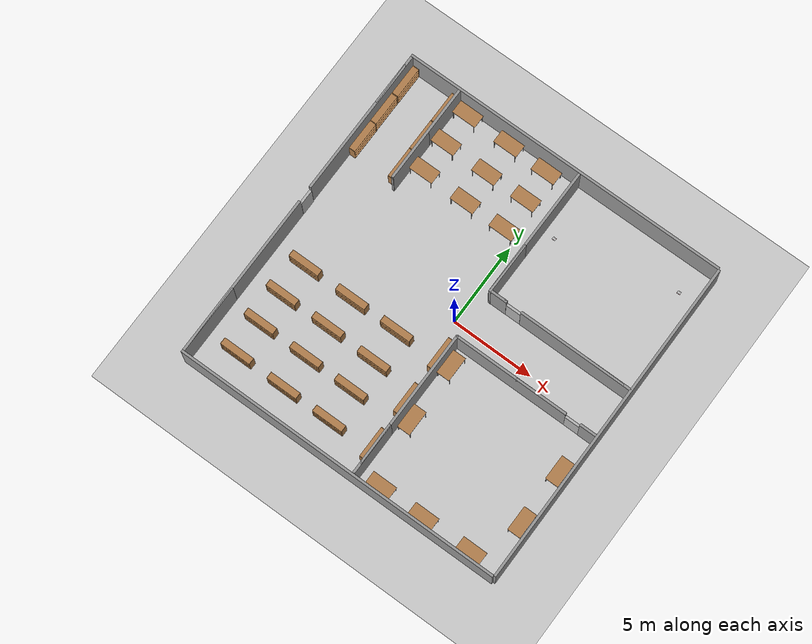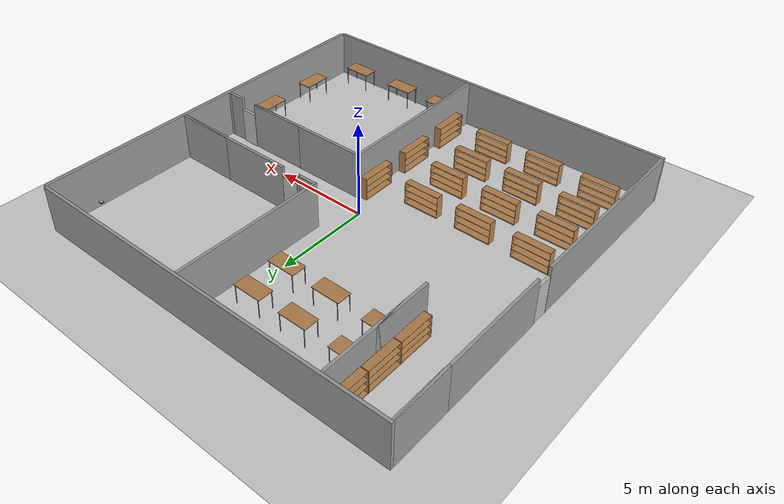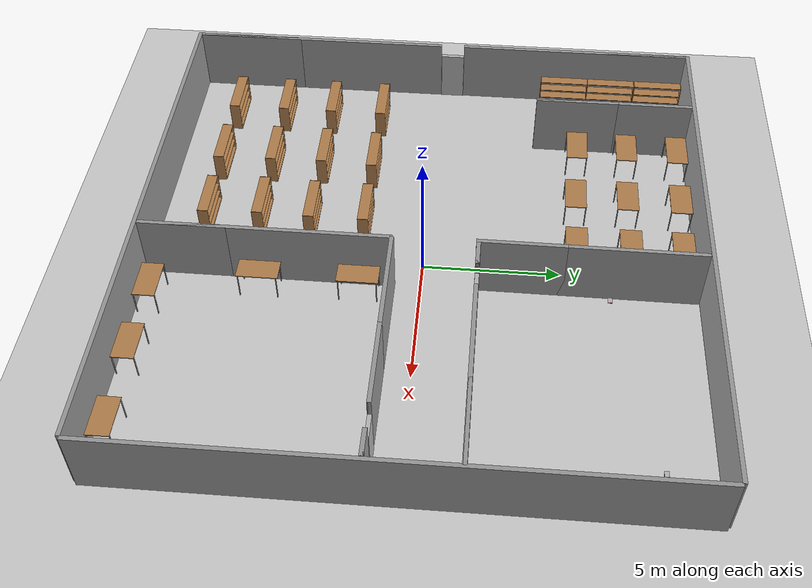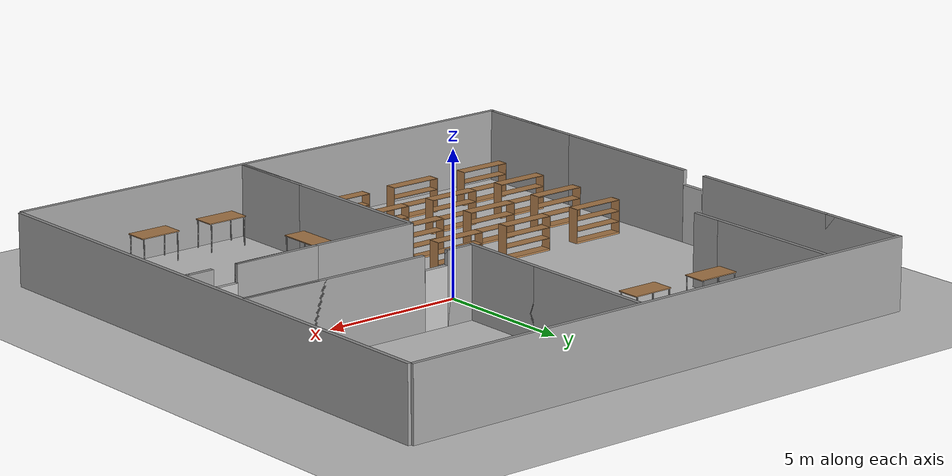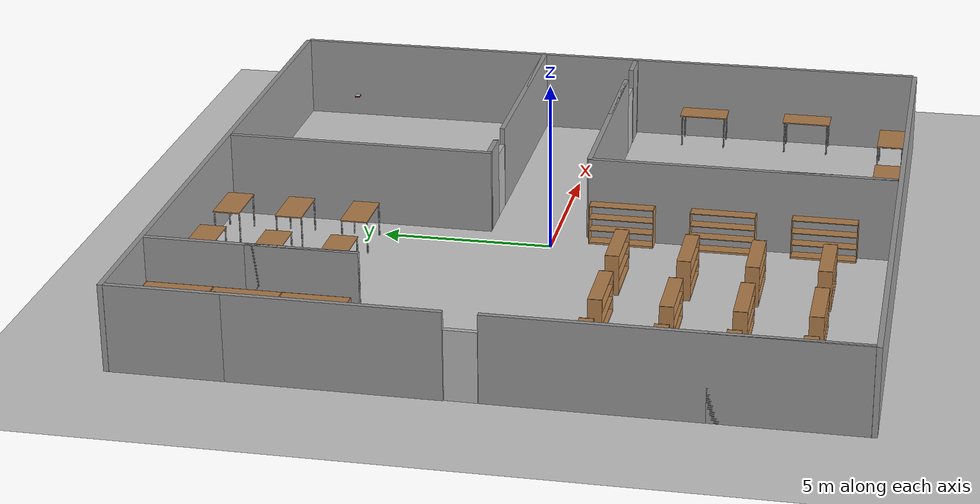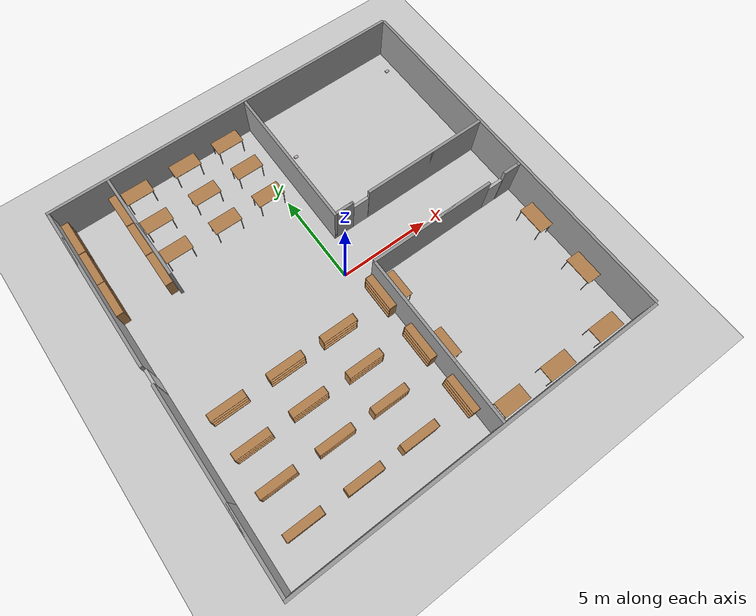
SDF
<sdf version="1.7">
 <world name="default">
  <model name="ground_plane">
   <static>1</static>
   <link name="link">
    <collision name="collision">
     <geometry><plane><normal>0 0 1</normal><size>100 100</size></plane></geometry>
     <surface>
      <contact><collide_bitmask>65535</collide_bitmask></contact>
      <friction><ode><mu>100</mu><mu2>50</mu2></ode></friction>
     </surface>
    </collision>
    <visual name="visual">
     <cast_shadows>0</cast_shadows>
     <geometry><plane><normal>0 0 1</normal><size>100 100</size></plane></geometry>
     <material>
      <script><uri>file://media/materials/scripts/gazebo.material</uri><name>Gazebo/Grey</name></script>
     </material>
    </visual>
   </link>
  </model>
  <gravity>0 0 -9.8</gravity>
  <magnetic_field>6e-06 2.3e-05 -4.2e-05</magnetic_field>
  <atmosphere type="adiabatic"/>
  <physics type="ode">
   <max_step_size>0.001</max_step_size>
   <real_time_factor>1</real_time_factor>
   <real_time_update_rate>1000</real_time_update_rate>
  </physics>
  <scene><ambient>0.4 0.4 0.4 1</ambient><background>0.7 0.7 0.7 1</background><shadows>1</shadows></scene>
  <spherical_coordinates>
   <surface_model>EARTH_WGS84</surface_model>
   <latitude_deg>0</latitude_deg>
   <longitude_deg>0</longitude_deg>
   <elevation>0</elevation>
   <heading_deg>0</heading_deg>
  </spherical_coordinates>
  <model name="wall_20m">
   <pose>10.3668 0.002945 0 0 -0 0</pose>
   <link name="Wall_0">
    <collision name="Wall_0_Collision">
     <geometry><box><size>20 0.15 2.5</size></box></geometry>
     <pose>0 0 1.25 0 -0 0</pose>
    </collision>
    <visual name="Wall_0_Visual">
     <pose>0 0 1.25 0 -0 0</pose>
     <geometry><box><size>20 0.15 2.5</size></box></geometry>
     <material>
      <script><uri>file://media/materials/scripts/gazebo.material</uri><name>Gazebo/Grey</name></script>
      <ambient>1 1 1 1</ambient>
     </material>
     <meta><layer>0</layer></meta>
    </visual>
    <pose>-0.482276 -0 0 0 -0 1.5708</pose>
   </link>
   <static>1</static>
  </model>
  <model name="wall_20m_0">
   <pose>-0.159869 9.52923 0 0 0 -1.56837</pose>
   <link name="Wall_0">
    <collision name="Wall_0_Collision">
     <geometry><box><size>20 0.15 2.5</size></box></geometry>
     <pose>0 0 1.25 0 -0 0</pose>
    </collision>
    <visual name="Wall_0_Visual">
     <pose>0 0 1.25 0 -0 0</pose>
     <geometry><box><size>20 0.15 2.5</size></box></geometry>
     <material>
      <script><uri>file://media/materials/scripts/gazebo.material</uri><name>Gazebo/Grey</name></script>
      <ambient>1 1 1 1</ambient>
     </material>
     <meta><layer>0</layer></meta>
    </visual>
    <pose>-0.482276 -0 0 0 -0 1.5708</pose>
   </link>
   <static>1</static>
  </model>
  <model name="wall_20m_0_clone">
   <pose>-0.174596 -10.5481 0 0 0 -1.56837</pose>
   <link name="Wall_0">
    <collision name="Wall_0_Collision">
     <geometry><box><size>20 0.15 2.5</size></box></geometry>
     <pose>0 0 1.25 0 -0 0</pose>
    </collision>
    <visual name="Wall_0_Visual">
     <pose>0 0 1.25 0 -0 0</pose>
     <geometry><box><size>20 0.15 2.5</size></box></geometry>
     <material>
      <script><uri>file://media/materials/scripts/gazebo.material</uri><name>Gazebo/Grey</name></script>
      <ambient>1 1 1 1</ambient>
     </material>
     <meta><layer>0</layer></meta>
    </visual>
    <pose>-0.482276 -0 0 0 -0 1.5708</pose>
   </link>
   <static>1</static>
  </model>
  <model name="wall_10m">
   <pose>-10.0955 -5.01191 0 0 0 -1.57203</pose>
   <link name="Wall_0">
    <collision name="Wall_0_Collision">
     <geometry><box><size>4.16 0.15 2.5</size></box></geometry>
     <pose>0 0 1.25 0 -0 0</pose>
    </collision>
    <visual name="Wall_0_Visual">
     <pose>0 0 1.25 0 -0 0</pose>
     <geometry><box><size>4.16 0.15 2.5</size></box></geometry>
     <material>
      <script><uri>file://media/materials/scripts/gazebo.material</uri><name>Gazebo/Grey</name></script>
      <ambient>1 1 1 1</ambient>
     </material>
     <meta><layer>0</layer></meta>
    </visual>
    <pose>2.92 0 0 0 -0 0</pose>
   </link>
   <link name="Wall_1">
    <collision name="Wall_1_Collision">
     <geometry><box><size>10 0.15 2.5</size></box></geometry>
     <pose>0 0 1.25 0 -0 0</pose>
    </collision>
    <visual name="Wall_1_Visual">
     <pose>0 0 1.25 0 -0 0</pose>
     <geometry><box><size>10 0.15 2.5</size></box></geometry>
     <material>
      <script><uri>file://media/materials/scripts/gazebo.material</uri><name>Gazebo/Grey</name></script>
      <ambient>1 1 1 1</ambient>
     </material>
     <meta><layer>0</layer></meta>
    </visual>
    <pose>0 0 0 0 -0 3.14159</pose>
   </link>
   <static>1</static>
  </model>
  <model name="door_1">
   <link name="link_0">
    <visual name="visual">
     <pose>0 0 1 0 -0 0</pose>
     <geometry><box><size>0.9 0.15 2</size></box></geometry>
     <material>
      <script>
       <uri>model://door/materials/scripts</uri>
       <uri>model://door/materials/textures</uri>
       <name>door</name>
      </script>
     </material>
    </visual>
    <collision name="collision">
     <pose>0 0 1 0 -0 0</pose>
     <geometry><box><size>0.9 0.15 2</size></box></geometry>
    </collision>
   </link>
   <static>1</static>
   <pose>-10.0824 0.449021 0 0 -0 1.568</pose>
  </model>
  <model name="wall_9m">
   <pose>-10.0971 5.40979 0 0 -0 1.56823</pose>
   <link name="Wall_0">
    <collision name="Wall_0_Collision">
     <geometry><box><size>3.16 0.15 2.5</size></box></geometry>
     <pose>0 0 1.25 0 -0 0</pose>
    </collision>
    <visual name="Wall_0_Visual">
     <pose>0 0 1.25 0 -0 0</pose>
     <geometry><box><size>3.16 0.15 2.5</size></box></geometry>
     <material>
      <script><uri>file://media/materials/scripts/gazebo.material</uri><name>Gazebo/Grey</name></script>
      <ambient>1 1 1 1</ambient>
     </material>
     <meta><layer>0</layer></meta>
    </visual>
    <pose>2.92 0 0 0 -0 0</pose>
   </link>
   <link name="Wall_1">
    <collision name="Wall_1_Collision">
     <geometry><box><size>9 0.15 2.5</size></box></geometry>
     <pose>0 0 1.25 0 -0 0</pose>
    </collision>
    <visual name="Wall_1_Visual">
     <pose>0 0 1.25 0 -0 0</pose>
     <geometry><box><size>9 0.15 2.5</size></box></geometry>
     <material>
      <script><uri>file://media/materials/scripts/gazebo.material</uri><name>Gazebo/Grey</name></script>
      <ambient>1 1 1 1</ambient>
     </material>
     <meta><layer>0</layer></meta>
    </visual>
    <pose>0 0 0 0 -0 3.14159</pose>
   </link>
   <static>1</static>
  </model>
  <model name="wall_9m_1">
   <pose>0.904043 -5.47693 0 0 0 -1.57385</pose>
   <link name="Wall_0">
    <collision name="Wall_0_Collision">
     <geometry><box><size>3.16 0.15 2.5</size></box></geometry>
     <pose>0 0 1.25 0 -0 0</pose>
    </collision>
    <visual name="Wall_0_Visual">
     <pose>0 0 1.25 0 -0 0</pose>
     <geometry><box><size>3.16 0.15 2.5</size></box></geometry>
     <material>
      <script><uri>file://media/materials/scripts/gazebo.material</uri><name>Gazebo/Grey</name></script>
      <ambient>1 1 1 1</ambient>
     </material>
     <meta><layer>0</layer></meta>
    </visual>
    <pose>2.92 0 0 0 -0 0</pose>
   </link>
   <link name="Wall_1">
    <collision name="Wall_1_Collision">
     <geometry><box><size>9 0.15 2.5</size></box></geometry>
     <pose>0 0 1.25 0 -0 0</pose>
    </collision>
    <visual name="Wall_1_Visual">
     <pose>0 0 1.25 0 -0 0</pose>
     <geometry><box><size>9 0.15 2.5</size></box></geometry>
     <material>
      <script><uri>file://media/materials/scripts/gazebo.material</uri><name>Gazebo/Grey</name></script>
      <ambient>1 1 1 1</ambient>
     </material>
     <meta><layer>0</layer></meta>
    </visual>
    <pose>0 0 0 0 -0 3.14159</pose>
   </link>
   <static>1</static>
  </model>
  <model name="door_1_0">
   <link name="link_0">
    <visual name="visual">
     <pose>0 0 1 0 -0 0</pose>
     <geometry><box><size>0.9 0.15 2</size></box></geometry>
     <material>
      <script>
       <uri>model://door/materials/scripts</uri>
       <uri>model://door/materials/textures</uri>
       <name>door</name>
      </script>
     </material>
    </visual>
    <collision name="collision">
     <pose>0 0 1 0 -0 0</pose>
     <geometry><box><size>0.9 0.15 2</size></box></geometry>
    </collision>
   </link>
   <static>1</static>
   <pose>2.39581 2.01305 0.003522 0 -0 0</pose>
  </model>
  <model name="door_1_1">
   <link name="link_0">
    <visual name="visual">
     <pose>0 0 1 0 -0 0</pose>
     <geometry><box><size>0.9 0.15 2</size></box></geometry>
     <material>
      <script>
       <uri>model://door/materials/scripts</uri>
       <uri>model://door/materials/textures</uri>
       <name>door</name>
      </script>
     </material>
    </visual>
    <collision name="collision">
     <pose>0 0 1 0 -0 0</pose>
     <geometry><box><size>0.9 0.15 2</size></box></geometry>
    </collision>
   </link>
   <static>1</static>
   <pose>8.35369 -1.00026 -0.114719 0 -0 0</pose>
  </model>
  <model name="wall_1m">
   <pose>1.43654 2.00733 0 0 -0 0</pose>
   <link name="Wall_0">
    <collision name="Wall_0_Collision">
     <geometry><box><size>0.16 0.15 2.5</size></box></geometry>
     <pose>0 0 1.25 0 -0 0</pose>
    </collision>
    <visual name="Wall_0_Visual">
     <pose>0 0 1.25 0 -0 0</pose>
     <geometry><box><size>0.16 0.15 2.5</size></box></geometry>
     <material>
      <script><uri>file://media/materials/scripts/gazebo.material</uri><name>Gazebo/Grey</name></script>
      <ambient>1 1 1 1</ambient>
     </material>
     <meta><layer>0</layer></meta>
    </visual>
    <pose>0.42 0 0 0 -0 0</pose>
   </link>
   <link name="Wall_1">
    <collision name="Wall_1_Collision">
     <geometry><box><size>1 0.15 2.5</size></box></geometry>
     <pose>0 0 1.25 0 -0 0</pose>
    </collision>
    <visual name="Wall_1_Visual">
     <pose>0 0 1.25 0 -0 0</pose>
     <geometry><box><size>1 0.15 2.5</size></box></geometry>
     <material>
      <script><uri>file://media/materials/scripts/gazebo.material</uri><name>Gazebo/Grey</name></script>
      <ambient>1 1 1 1</ambient>
     </material>
     <meta><layer>0</layer></meta>
    </visual>
    <pose>0 0 0 0 -0 3.14159</pose>
   </link>
   <static>1</static>
  </model>
  <model name="wall_1m_0">
   <pose>9.30672 -1.01779 0 0 -0 0</pose>
   <link name="Wall_0">
    <collision name="Wall_0_Collision">
     <geometry><box><size>0.16 0.15 2.5</size></box></geometry>
     <pose>0 0 1.25 0 -0 0</pose>
    </collision>
    <visual name="Wall_0_Visual">
     <pose>0 0 1.25 0 -0 0</pose>
     <geometry><box><size>0.16 0.15 2.5</size></box></geometry>
     <material>
      <script><uri>file://media/materials/scripts/gazebo.material</uri><name>Gazebo/Grey</name></script>
      <ambient>1 1 1 1</ambient>
     </material>
     <meta><layer>0</layer></meta>
    </visual>
    <pose>0.42 0 0 0 -0 0</pose>
   </link>
   <link name="Wall_1">
    <collision name="Wall_1_Collision">
     <geometry><box><size>1 0.15 2.5</size></box></geometry>
     <pose>0 0 1.25 0 -0 0</pose>
    </collision>
    <visual name="Wall_1_Visual">
     <pose>0 0 1.25 0 -0 0</pose>
     <geometry><box><size>1 0.15 2.5</size></box></geometry>
     <material>
      <script><uri>file://media/materials/scripts/gazebo.material</uri><name>Gazebo/Grey</name></script>
      <ambient>1 1 1 1</ambient>
     </material>
     <meta><layer>0</layer></meta>
    </visual>
    <pose>0 0 0 0 -0 3.14159</pose>
   </link>
   <static>1</static>
  </model>
  <model name="wall_7m">
   <pose>4.40112 -1.00406 0 0 -0 0</pose>
   <link name="Wall_0">
    <collision name="Wall_0_Collision">
     <geometry><box><size>3.16 0.15 2.5</size></box></geometry>
     <pose>0 0 1.25 0 -0 0</pose>
    </collision>
    <visual name="Wall_0_Visual">
     <pose>0 0 1.25 0 -0 0</pose>
     <geometry><box><size>3.16 0.15 2.5</size></box></geometry>
     <material>
      <script><uri>file://media/materials/scripts/gazebo.material</uri><name>Gazebo/Grey</name></script>
      <ambient>1 1 1 1</ambient>
     </material>
     <meta><layer>0</layer></meta>
    </visual>
    <pose>1.92 0 0 0 -0 0</pose>
   </link>
   <link name="Wall_1">
    <collision name="Wall_1_Collision">
     <geometry><box><size>7 0.15 2.5</size></box></geometry>
     <pose>0 0 1.25 0 -0 0</pose>
    </collision>
    <visual name="Wall_1_Visual">
     <pose>0 0 1.25 0 -0 0</pose>
     <geometry><box><size>7 0.15 2.5</size></box></geometry>
     <material>
      <script><uri>file://media/materials/scripts/gazebo.material</uri><name>Gazebo/Grey</name></script>
      <ambient>1 1 1 1</ambient>
     </material>
     <meta><layer>0</layer></meta>
    </visual>
    <pose>0 0 0 0 -0 3.14159</pose>
   </link>
   <static>1</static>
  </model>
  <model name="wall_7m_0">
   <pose>6.35669 2.00921 0 0 -0 0</pose>
   <link name="Wall_0">
    <collision name="Wall_0_Collision">
     <geometry><box><size>3.16 0.15 2.5</size></box></geometry>
     <pose>0 0 1.25 0 -0 0</pose>
    </collision>
    <visual name="Wall_0_Visual">
     <pose>0 0 1.25 0 -0 0</pose>
     <geometry><box><size>3.16 0.15 2.5</size></box></geometry>
     <material>
      <script><uri>file://media/materials/scripts/gazebo.material</uri><name>Gazebo/Grey</name></script>
      <ambient>1 1 1 1</ambient>
     </material>
     <meta><layer>0</layer></meta>
    </visual>
    <pose>1.92 0 0 0 -0 0</pose>
   </link>
   <link name="Wall_1">
    <collision name="Wall_1_Collision">
     <geometry><box><size>7 0.15 2.5</size></box></geometry>
     <pose>0 0 1.25 0 -0 0</pose>
    </collision>
    <visual name="Wall_1_Visual">
     <pose>0 0 1.25 0 -0 0</pose>
     <geometry><box><size>7 0.15 2.5</size></box></geometry>
     <material>
      <script><uri>file://media/materials/scripts/gazebo.material</uri><name>Gazebo/Grey</name></script>
      <ambient>1 1 1 1</ambient>
     </material>
     <meta><layer>0</layer></meta>
    </visual>
    <pose>0 0 0 0 -0 3.14159</pose>
   </link>
   <static>1</static>
  </model>
  <model name="bookshelf_twosided">
   <static>1</static>
   <link name="link">
    <inertial><mass>1</mass></inertial>
    <collision name="left_side">
     <pose>0.95 -0.195 0.6 0 -0 0</pose>
     <geometry><box><size>0.02 0.4 1.2</size></box></geometry>
    </collision>
    <visual name="left_side">
     <pose>0.95 -0.195 0.6 0 -0 0</pose>
     <geometry><box><size>0.02 0.4 1.2</size></box></geometry>
     <material>
      <script><uri>file://media/materials/scripts/gazebo.material</uri><name>Gazebo/Wood</name></script>
     </material>
    </visual>
    <collision name="right_side">
     <pose>-0.95 -0.195 0.6 0 -0 0</pose>
     <geometry><box><size>0.02 0.4 1.2</size></box></geometry>
    </collision>
    <visual name="right_side">
     <pose>-0.95 -0.195 0.6 0 -0 0</pose>
     <geometry><box><size>0.02 0.4 1.2</size></box></geometry>
     <material>
      <script><uri>file://media/materials/scripts/gazebo.material</uri><name>Gazebo/Wood</name></script>
     </material>
    </visual>
    <collision name="bottom">
     <pose>0 -0.195 0.03 0 -0 0</pose>
     <geometry><box><size>1.88 0.4 0.06</size></box></geometry>
    </collision>
    <visual name="bottom">
     <pose>0 -0.195 0.03 0 -0 0</pose>
     <geometry><box><size>1.88 0.4 0.06</size></box></geometry>
     <material>
      <script><uri>file://media/materials/scripts/gazebo.material</uri><name>Gazebo/Wood</name></script>
     </material>
    </visual>
    <collision name="top">
     <pose>0 -0.195 1.19 0 -0 0</pose>
     <geometry><box><size>1.88 0.4 0.02</size></box></geometry>
    </collision>
    <visual name="top">
     <pose>0 -0.195 1.19 0 -0 0</pose>
     <geometry><box><size>1.88 0.4 0.02</size></box></geometry>
     <material>
      <script><uri>file://media/materials/scripts/gazebo.material</uri><name>Gazebo/Wood</name></script>
     </material>
    </visual>
    <collision name="low_shelf">
     <pose>0 -0.195 0.43 0 -0 0</pose>
     <geometry><box><size>1.88 0.4 0.02</size></box></geometry>
    </collision>
    <visual name="low_shelf">
     <pose>0 -0.195 0.43 0 -0 0</pose>
     <geometry><box><size>1.88 0.4 0.02</size></box></geometry>
     <material>
      <script><uri>file://media/materials/scripts/gazebo.material</uri><name>Gazebo/Wood</name></script>
     </material>
    </visual>
    <collision name="high_shelf">
     <pose>0 -0.195 0.8 0 -0 0</pose>
     <geometry><box><size>1.88 0.4 0.02</size></box></geometry>
    </collision>
    <visual name="high_shelf">
     <pose>0 -0.195 0.8 0 -0 0</pose>
     <geometry><box><size>1.88 0.4 0.02</size></box></geometry>
     <material>
      <script><uri>file://media/materials/scripts/gazebo.material</uri><name>Gazebo/Wood</name></script>
     </material>
    </visual>
   </link>
   <pose>-8.08838 -8.03725 0 0 -0 0</pose>
  </model>
  <model name="bookshelf_twosided_0">
   <static>1</static>
   <link name="link">
    <inertial><mass>1</mass></inertial>
    <collision name="left_side">
     <pose>0.95 -0.195 0.6 0 -0 0</pose>
     <geometry><box><size>0.02 0.4 1.2</size></box></geometry>
    </collision>
    <visual name="left_side">
     <pose>0.95 -0.195 0.6 0 -0 0</pose>
     <geometry><box><size>0.02 0.4 1.2</size></box></geometry>
     <material>
      <script><uri>file://media/materials/scripts/gazebo.material</uri><name>Gazebo/Wood</name></script>
     </material>
    </visual>
    <collision name="right_side">
     <pose>-0.95 -0.195 0.6 0 -0 0</pose>
     <geometry><box><size>0.02 0.4 1.2</size></box></geometry>
    </collision>
    <visual name="right_side">
     <pose>-0.95 -0.195 0.6 0 -0 0</pose>
     <geometry><box><size>0.02 0.4 1.2</size></box></geometry>
     <material>
      <script><uri>file://media/materials/scripts/gazebo.material</uri><name>Gazebo/Wood</name></script>
     </material>
    </visual>
    <collision name="bottom">
     <pose>0 -0.195 0.03 0 -0 0</pose>
     <geometry><box><size>1.88 0.4 0.06</size></box></geometry>
    </collision>
    <visual name="bottom">
     <pose>0 -0.195 0.03 0 -0 0</pose>
     <geometry><box><size>1.88 0.4 0.06</size></box></geometry>
     <material>
      <script><uri>file://media/materials/scripts/gazebo.material</uri><name>Gazebo/Wood</name></script>
     </material>
    </visual>
    <collision name="top">
     <pose>0 -0.195 1.19 0 -0 0</pose>
     <geometry><box><size>1.88 0.4 0.02</size></box></geometry>
    </collision>
    <visual name="top">
     <pose>0 -0.195 1.19 0 -0 0</pose>
     <geometry><box><size>1.88 0.4 0.02</size></box></geometry>
     <material>
      <script><uri>file://media/materials/scripts/gazebo.material</uri><name>Gazebo/Wood</name></script>
     </material>
    </visual>
    <collision name="low_shelf">
     <pose>0 -0.195 0.43 0 -0 0</pose>
     <geometry><box><size>1.88 0.4 0.02</size></box></geometry>
    </collision>
    <visual name="low_shelf">
     <pose>0 -0.195 0.43 0 -0 0</pose>
     <geometry><box><size>1.88 0.4 0.02</size></box></geometry>
     <material>
      <script><uri>file://media/materials/scripts/gazebo.material</uri><name>Gazebo/Wood</name></script>
     </material>
    </visual>
    <collision name="high_shelf">
     <pose>0 -0.195 0.8 0 -0 0</pose>
     <geometry><box><size>1.88 0.4 0.02</size></box></geometry>
    </collision>
    <visual name="high_shelf">
     <pose>0 -0.195 0.8 0 -0 0</pose>
     <geometry><box><size>1.88 0.4 0.02</size></box></geometry>
     <material>
      <script><uri>file://media/materials/scripts/gazebo.material</uri><name>Gazebo/Wood</name></script>
     </material>
    </visual>
   </link>
   <pose>-5.00919 -8.07152 0 0 -0 0</pose>
  </model>
  <model name="bookshelf_twosided_1">
   <static>1</static>
   <link name="link">
    <inertial><mass>1</mass></inertial>
    <collision name="left_side">
     <pose>0.95 -0.195 0.6 0 -0 0</pose>
     <geometry><box><size>0.02 0.4 1.2</size></box></geometry>
    </collision>
    <visual name="left_side">
     <pose>0.95 -0.195 0.6 0 -0 0</pose>
     <geometry><box><size>0.02 0.4 1.2</size></box></geometry>
     <material>
      <script><uri>file://media/materials/scripts/gazebo.material</uri><name>Gazebo/Wood</name></script>
     </material>
    </visual>
    <collision name="right_side">
     <pose>-0.95 -0.195 0.6 0 -0 0</pose>
     <geometry><box><size>0.02 0.4 1.2</size></box></geometry>
    </collision>
    <visual name="right_side">
     <pose>-0.95 -0.195 0.6 0 -0 0</pose>
     <geometry><box><size>0.02 0.4 1.2</size></box></geometry>
     <material>
      <script><uri>file://media/materials/scripts/gazebo.material</uri><name>Gazebo/Wood</name></script>
     </material>
    </visual>
    <collision name="bottom">
     <pose>0 -0.195 0.03 0 -0 0</pose>
     <geometry><box><size>1.88 0.4 0.06</size></box></geometry>
    </collision>
    <visual name="bottom">
     <pose>0 -0.195 0.03 0 -0 0</pose>
     <geometry><box><size>1.88 0.4 0.06</size></box></geometry>
     <material>
      <script><uri>file://media/materials/scripts/gazebo.material</uri><name>Gazebo/Wood</name></script>
     </material>
    </visual>
    <collision name="top">
     <pose>0 -0.195 1.19 0 -0 0</pose>
     <geometry><box><size>1.88 0.4 0.02</size></box></geometry>
    </collision>
    <visual name="top">
     <pose>0 -0.195 1.19 0 -0 0</pose>
     <geometry><box><size>1.88 0.4 0.02</size></box></geometry>
     <material>
      <script><uri>file://media/materials/scripts/gazebo.material</uri><name>Gazebo/Wood</name></script>
     </material>
    </visual>
    <collision name="low_shelf">
     <pose>0 -0.195 0.43 0 -0 0</pose>
     <geometry><box><size>1.88 0.4 0.02</size></box></geometry>
    </collision>
    <visual name="low_shelf">
     <pose>0 -0.195 0.43 0 -0 0</pose>
     <geometry><box><size>1.88 0.4 0.02</size></box></geometry>
     <material>
      <script><uri>file://media/materials/scripts/gazebo.material</uri><name>Gazebo/Wood</name></script>
     </material>
    </visual>
    <collision name="high_shelf">
     <pose>0 -0.195 0.8 0 -0 0</pose>
     <geometry><box><size>1.88 0.4 0.02</size></box></geometry>
    </collision>
    <visual name="high_shelf">
     <pose>0 -0.195 0.8 0 -0 0</pose>
     <geometry><box><size>1.88 0.4 0.02</size></box></geometry>
     <material>
      <script><uri>file://media/materials/scripts/gazebo.material</uri><name>Gazebo/Wood</name></script>
     </material>
    </visual>
   </link>
   <pose>-2.03359 -8.06213 0 0 -0 0</pose>
  </model>
  <model name="bookshelf_twosided_2">
   <static>1</static>
   <link name="link">
    <inertial><mass>1</mass></inertial>
    <collision name="left_side">
     <pose>0.95 -0.195 0.6 0 -0 0</pose>
     <geometry><box><size>0.02 0.4 1.2</size></box></geometry>
    </collision>
    <visual name="left_side">
     <pose>0.95 -0.195 0.6 0 -0 0</pose>
     <geometry><box><size>0.02 0.4 1.2</size></box></geometry>
     <material>
      <script><uri>file://media/materials/scripts/gazebo.material</uri><name>Gazebo/Wood</name></script>
     </material>
    </visual>
    <collision name="right_side">
     <pose>-0.95 -0.195 0.6 0 -0 0</pose>
     <geometry><box><size>0.02 0.4 1.2</size></box></geometry>
    </collision>
    <visual name="right_side">
     <pose>-0.95 -0.195 0.6 0 -0 0</pose>
     <geometry><box><size>0.02 0.4 1.2</size></box></geometry>
     <material>
      <script><uri>file://media/materials/scripts/gazebo.material</uri><name>Gazebo/Wood</name></script>
     </material>
    </visual>
    <collision name="bottom">
     <pose>0 -0.195 0.03 0 -0 0</pose>
     <geometry><box><size>1.88 0.4 0.06</size></box></geometry>
    </collision>
    <visual name="bottom">
     <pose>0 -0.195 0.03 0 -0 0</pose>
     <geometry><box><size>1.88 0.4 0.06</size></box></geometry>
     <material>
      <script><uri>file://media/materials/scripts/gazebo.material</uri><name>Gazebo/Wood</name></script>
     </material>
    </visual>
    <collision name="top">
     <pose>0 -0.195 1.19 0 -0 0</pose>
     <geometry><box><size>1.88 0.4 0.02</size></box></geometry>
    </collision>
    <visual name="top">
     <pose>0 -0.195 1.19 0 -0 0</pose>
     <geometry><box><size>1.88 0.4 0.02</size></box></geometry>
     <material>
      <script><uri>file://media/materials/scripts/gazebo.material</uri><name>Gazebo/Wood</name></script>
     </material>
    </visual>
    <collision name="low_shelf">
     <pose>0 -0.195 0.43 0 -0 0</pose>
     <geometry><box><size>1.88 0.4 0.02</size></box></geometry>
    </collision>
    <visual name="low_shelf">
     <pose>0 -0.195 0.43 0 -0 0</pose>
     <geometry><box><size>1.88 0.4 0.02</size></box></geometry>
     <material>
      <script><uri>file://media/materials/scripts/gazebo.material</uri><name>Gazebo/Wood</name></script>
     </material>
    </visual>
    <collision name="high_shelf">
     <pose>0 -0.195 0.8 0 -0 0</pose>
     <geometry><box><size>1.88 0.4 0.02</size></box></geometry>
    </collision>
    <visual name="high_shelf">
     <pose>0 -0.195 0.8 0 -0 0</pose>
     <geometry><box><size>1.88 0.4 0.02</size></box></geometry>
     <material>
      <script><uri>file://media/materials/scripts/gazebo.material</uri><name>Gazebo/Wood</name></script>
     </material>
    </visual>
   </link>
   <pose>-8.0795 -6.02858 0 0 -0 0</pose>
  </model>
  <model name="bookshelf_twosided_3">
   <static>1</static>
   <link name="link">
    <inertial><mass>1</mass></inertial>
    <collision name="left_side">
     <pose>0.95 -0.195 0.6 0 -0 0</pose>
     <geometry><box><size>0.02 0.4 1.2</size></box></geometry>
    </collision>
    <visual name="left_side">
     <pose>0.95 -0.195 0.6 0 -0 0</pose>
     <geometry><box><size>0.02 0.4 1.2</size></box></geometry>
     <material>
      <script><uri>file://media/materials/scripts/gazebo.material</uri><name>Gazebo/Wood</name></script>
     </material>
    </visual>
    <collision name="right_side">
     <pose>-0.95 -0.195 0.6 0 -0 0</pose>
     <geometry><box><size>0.02 0.4 1.2</size></box></geometry>
    </collision>
    <visual name="right_side">
     <pose>-0.95 -0.195 0.6 0 -0 0</pose>
     <geometry><box><size>0.02 0.4 1.2</size></box></geometry>
     <material>
      <script><uri>file://media/materials/scripts/gazebo.material</uri><name>Gazebo/Wood</name></script>
     </material>
    </visual>
    <collision name="bottom">
     <pose>0 -0.195 0.03 0 -0 0</pose>
     <geometry><box><size>1.88 0.4 0.06</size></box></geometry>
    </collision>
    <visual name="bottom">
     <pose>0 -0.195 0.03 0 -0 0</pose>
     <geometry><box><size>1.88 0.4 0.06</size></box></geometry>
     <material>
      <script><uri>file://media/materials/scripts/gazebo.material</uri><name>Gazebo/Wood</name></script>
     </material>
    </visual>
    <collision name="top">
     <pose>0 -0.195 1.19 0 -0 0</pose>
     <geometry><box><size>1.88 0.4 0.02</size></box></geometry>
    </collision>
    <visual name="top">
     <pose>0 -0.195 1.19 0 -0 0</pose>
     <geometry><box><size>1.88 0.4 0.02</size></box></geometry>
     <material>
      <script><uri>file://media/materials/scripts/gazebo.material</uri><name>Gazebo/Wood</name></script>
     </material>
    </visual>
    <collision name="low_shelf">
     <pose>0 -0.195 0.43 0 -0 0</pose>
     <geometry><box><size>1.88 0.4 0.02</size></box></geometry>
    </collision>
    <visual name="low_shelf">
     <pose>0 -0.195 0.43 0 -0 0</pose>
     <geometry><box><size>1.88 0.4 0.02</size></box></geometry>
     <material>
      <script><uri>file://media/materials/scripts/gazebo.material</uri><name>Gazebo/Wood</name></script>
     </material>
    </visual>
    <collision name="high_shelf">
     <pose>0 -0.195 0.8 0 -0 0</pose>
     <geometry><box><size>1.88 0.4 0.02</size></box></geometry>
    </collision>
    <visual name="high_shelf">
     <pose>0 -0.195 0.8 0 -0 0</pose>
     <geometry><box><size>1.88 0.4 0.02</size></box></geometry>
     <material>
      <script><uri>file://media/materials/scripts/gazebo.material</uri><name>Gazebo/Wood</name></script>
     </material>
    </visual>
   </link>
   <pose>-5.05887 -6.04865 0 0 -0 0</pose>
  </model>
  <model name="bookshelf_twosided_4">
   <static>1</static>
   <link name="link">
    <inertial><mass>1</mass></inertial>
    <collision name="left_side">
     <pose>0.95 -0.195 0.6 0 -0 0</pose>
     <geometry><box><size>0.02 0.4 1.2</size></box></geometry>
    </collision>
    <visual name="left_side">
     <pose>0.95 -0.195 0.6 0 -0 0</pose>
     <geometry><box><size>0.02 0.4 1.2</size></box></geometry>
     <material>
      <script><uri>file://media/materials/scripts/gazebo.material</uri><name>Gazebo/Wood</name></script>
     </material>
    </visual>
    <collision name="right_side">
     <pose>-0.95 -0.195 0.6 0 -0 0</pose>
     <geometry><box><size>0.02 0.4 1.2</size></box></geometry>
    </collision>
    <visual name="right_side">
     <pose>-0.95 -0.195 0.6 0 -0 0</pose>
     <geometry><box><size>0.02 0.4 1.2</size></box></geometry>
     <material>
      <script><uri>file://media/materials/scripts/gazebo.material</uri><name>Gazebo/Wood</name></script>
     </material>
    </visual>
    <collision name="bottom">
     <pose>0 -0.195 0.03 0 -0 0</pose>
     <geometry><box><size>1.88 0.4 0.06</size></box></geometry>
    </collision>
    <visual name="bottom">
     <pose>0 -0.195 0.03 0 -0 0</pose>
     <geometry><box><size>1.88 0.4 0.06</size></box></geometry>
     <material>
      <script><uri>file://media/materials/scripts/gazebo.material</uri><name>Gazebo/Wood</name></script>
     </material>
    </visual>
    <collision name="top">
     <pose>0 -0.195 1.19 0 -0 0</pose>
     <geometry><box><size>1.88 0.4 0.02</size></box></geometry>
    </collision>
    <visual name="top">
     <pose>0 -0.195 1.19 0 -0 0</pose>
     <geometry><box><size>1.88 0.4 0.02</size></box></geometry>
     <material>
      <script><uri>file://media/materials/scripts/gazebo.material</uri><name>Gazebo/Wood</name></script>
     </material>
    </visual>
    <collision name="low_shelf">
     <pose>0 -0.195 0.43 0 -0 0</pose>
     <geometry><box><size>1.88 0.4 0.02</size></box></geometry>
    </collision>
    <visual name="low_shelf">
     <pose>0 -0.195 0.43 0 -0 0</pose>
     <geometry><box><size>1.88 0.4 0.02</size></box></geometry>
     <material>
      <script><uri>file://media/materials/scripts/gazebo.material</uri><name>Gazebo/Wood</name></script>
     </material>
    </visual>
    <collision name="high_shelf">
     <pose>0 -0.195 0.8 0 -0 0</pose>
     <geometry><box><size>1.88 0.4 0.02</size></box></geometry>
    </collision>
    <visual name="high_shelf">
     <pose>0 -0.195 0.8 0 -0 0</pose>
     <geometry><box><size>1.88 0.4 0.02</size></box></geometry>
     <material>
      <script><uri>file://media/materials/scripts/gazebo.material</uri><name>Gazebo/Wood</name></script>
     </material>
    </visual>
   </link>
   <pose>-2.11262 -6.05427 0 0 -0 0</pose>
  </model>
  <model name="bookshelf_twosided_5">
   <static>1</static>
   <link name="link">
    <inertial><mass>1</mass></inertial>
    <collision name="left_side">
     <pose>0.95 -0.195 0.6 0 -0 0</pose>
     <geometry><box><size>0.02 0.4 1.2</size></box></geometry>
    </collision>
    <visual name="left_side">
     <pose>0.95 -0.195 0.6 0 -0 0</pose>
     <geometry><box><size>0.02 0.4 1.2</size></box></geometry>
     <material>
      <script><uri>file://media/materials/scripts/gazebo.material</uri><name>Gazebo/Wood</name></script>
     </material>
    </visual>
    <collision name="right_side">
     <pose>-0.95 -0.195 0.6 0 -0 0</pose>
     <geometry><box><size>0.02 0.4 1.2</size></box></geometry>
    </collision>
    <visual name="right_side">
     <pose>-0.95 -0.195 0.6 0 -0 0</pose>
     <geometry><box><size>0.02 0.4 1.2</size></box></geometry>
     <material>
      <script><uri>file://media/materials/scripts/gazebo.material</uri><name>Gazebo/Wood</name></script>
     </material>
    </visual>
    <collision name="bottom">
     <pose>0 -0.195 0.03 0 -0 0</pose>
     <geometry><box><size>1.88 0.4 0.06</size></box></geometry>
    </collision>
    <visual name="bottom">
     <pose>0 -0.195 0.03 0 -0 0</pose>
     <geometry><box><size>1.88 0.4 0.06</size></box></geometry>
     <material>
      <script><uri>file://media/materials/scripts/gazebo.material</uri><name>Gazebo/Wood</name></script>
     </material>
    </visual>
    <collision name="top">
     <pose>0 -0.195 1.19 0 -0 0</pose>
     <geometry><box><size>1.88 0.4 0.02</size></box></geometry>
    </collision>
    <visual name="top">
     <pose>0 -0.195 1.19 0 -0 0</pose>
     <geometry><box><size>1.88 0.4 0.02</size></box></geometry>
     <material>
      <script><uri>file://media/materials/scripts/gazebo.material</uri><name>Gazebo/Wood</name></script>
     </material>
    </visual>
    <collision name="low_shelf">
     <pose>0 -0.195 0.43 0 -0 0</pose>
     <geometry><box><size>1.88 0.4 0.02</size></box></geometry>
    </collision>
    <visual name="low_shelf">
     <pose>0 -0.195 0.43 0 -0 0</pose>
     <geometry><box><size>1.88 0.4 0.02</size></box></geometry>
     <material>
      <script><uri>file://media/materials/scripts/gazebo.material</uri><name>Gazebo/Wood</name></script>
     </material>
    </visual>
    <collision name="high_shelf">
     <pose>0 -0.195 0.8 0 -0 0</pose>
     <geometry><box><size>1.88 0.4 0.02</size></box></geometry>
    </collision>
    <visual name="high_shelf">
     <pose>0 -0.195 0.8 0 -0 0</pose>
     <geometry><box><size>1.88 0.4 0.02</size></box></geometry>
     <material>
      <script><uri>file://media/materials/scripts/gazebo.material</uri><name>Gazebo/Wood</name></script>
     </material>
    </visual>
   </link>
   <pose>-8.08114 -4.10736 0 0 -0 0</pose>
  </model>
  <model name="bookshelf_twosided_6">
   <static>1</static>
   <link name="link">
    <inertial><mass>1</mass></inertial>
    <collision name="left_side">
     <pose>0.95 -0.195 0.6 0 -0 0</pose>
     <geometry><box><size>0.02 0.4 1.2</size></box></geometry>
    </collision>
    <visual name="left_side">
     <pose>0.95 -0.195 0.6 0 -0 0</pose>
     <geometry><box><size>0.02 0.4 1.2</size></box></geometry>
     <material>
      <script><uri>file://media/materials/scripts/gazebo.material</uri><name>Gazebo/Wood</name></script>
     </material>
    </visual>
    <collision name="right_side">
     <pose>-0.95 -0.195 0.6 0 -0 0</pose>
     <geometry><box><size>0.02 0.4 1.2</size></box></geometry>
    </collision>
    <visual name="right_side">
     <pose>-0.95 -0.195 0.6 0 -0 0</pose>
     <geometry><box><size>0.02 0.4 1.2</size></box></geometry>
     <material>
      <script><uri>file://media/materials/scripts/gazebo.material</uri><name>Gazebo/Wood</name></script>
     </material>
    </visual>
    <collision name="bottom">
     <pose>0 -0.195 0.03 0 -0 0</pose>
     <geometry><box><size>1.88 0.4 0.06</size></box></geometry>
    </collision>
    <visual name="bottom">
     <pose>0 -0.195 0.03 0 -0 0</pose>
     <geometry><box><size>1.88 0.4 0.06</size></box></geometry>
     <material>
      <script><uri>file://media/materials/scripts/gazebo.material</uri><name>Gazebo/Wood</name></script>
     </material>
    </visual>
    <collision name="top">
     <pose>0 -0.195 1.19 0 -0 0</pose>
     <geometry><box><size>1.88 0.4 0.02</size></box></geometry>
    </collision>
    <visual name="top">
     <pose>0 -0.195 1.19 0 -0 0</pose>
     <geometry><box><size>1.88 0.4 0.02</size></box></geometry>
     <material>
      <script><uri>file://media/materials/scripts/gazebo.material</uri><name>Gazebo/Wood</name></script>
     </material>
    </visual>
    <collision name="low_shelf">
     <pose>0 -0.195 0.43 0 -0 0</pose>
     <geometry><box><size>1.88 0.4 0.02</size></box></geometry>
    </collision>
    <visual name="low_shelf">
     <pose>0 -0.195 0.43 0 -0 0</pose>
     <geometry><box><size>1.88 0.4 0.02</size></box></geometry>
     <material>
      <script><uri>file://media/materials/scripts/gazebo.material</uri><name>Gazebo/Wood</name></script>
     </material>
    </visual>
    <collision name="high_shelf">
     <pose>0 -0.195 0.8 0 -0 0</pose>
     <geometry><box><size>1.88 0.4 0.02</size></box></geometry>
    </collision>
    <visual name="high_shelf">
     <pose>0 -0.195 0.8 0 -0 0</pose>
     <geometry><box><size>1.88 0.4 0.02</size></box></geometry>
     <material>
      <script><uri>file://media/materials/scripts/gazebo.material</uri><name>Gazebo/Wood</name></script>
     </material>
    </visual>
   </link>
   <pose>-5.09321 -4.07593 0 0 -0 0</pose>
  </model>
  <model name="bookshelf_twosided_7">
   <static>1</static>
   <link name="link">
    <inertial><mass>1</mass></inertial>
    <collision name="left_side">
     <pose>0.95 -0.195 0.6 0 -0 0</pose>
     <geometry><box><size>0.02 0.4 1.2</size></box></geometry>
    </collision>
    <visual name="left_side">
     <pose>0.95 -0.195 0.6 0 -0 0</pose>
     <geometry><box><size>0.02 0.4 1.2</size></box></geometry>
     <material>
      <script><uri>file://media/materials/scripts/gazebo.material</uri><name>Gazebo/Wood</name></script>
     </material>
    </visual>
    <collision name="right_side">
     <pose>-0.95 -0.195 0.6 0 -0 0</pose>
     <geometry><box><size>0.02 0.4 1.2</size></box></geometry>
    </collision>
    <visual name="right_side">
     <pose>-0.95 -0.195 0.6 0 -0 0</pose>
     <geometry><box><size>0.02 0.4 1.2</size></box></geometry>
     <material>
      <script><uri>file://media/materials/scripts/gazebo.material</uri><name>Gazebo/Wood</name></script>
     </material>
    </visual>
    <collision name="bottom">
     <pose>0 -0.195 0.03 0 -0 0</pose>
     <geometry><box><size>1.88 0.4 0.06</size></box></geometry>
    </collision>
    <visual name="bottom">
     <pose>0 -0.195 0.03 0 -0 0</pose>
     <geometry><box><size>1.88 0.4 0.06</size></box></geometry>
     <material>
      <script><uri>file://media/materials/scripts/gazebo.material</uri><name>Gazebo/Wood</name></script>
     </material>
    </visual>
    <collision name="top">
     <pose>0 -0.195 1.19 0 -0 0</pose>
     <geometry><box><size>1.88 0.4 0.02</size></box></geometry>
    </collision>
    <visual name="top">
     <pose>0 -0.195 1.19 0 -0 0</pose>
     <geometry><box><size>1.88 0.4 0.02</size></box></geometry>
     <material>
      <script><uri>file://media/materials/scripts/gazebo.material</uri><name>Gazebo/Wood</name></script>
     </material>
    </visual>
    <collision name="low_shelf">
     <pose>0 -0.195 0.43 0 -0 0</pose>
     <geometry><box><size>1.88 0.4 0.02</size></box></geometry>
    </collision>
    <visual name="low_shelf">
     <pose>0 -0.195 0.43 0 -0 0</pose>
     <geometry><box><size>1.88 0.4 0.02</size></box></geometry>
     <material>
      <script><uri>file://media/materials/scripts/gazebo.material</uri><name>Gazebo/Wood</name></script>
     </material>
    </visual>
    <collision name="high_shelf">
     <pose>0 -0.195 0.8 0 -0 0</pose>
     <geometry><box><size>1.88 0.4 0.02</size></box></geometry>
    </collision>
    <visual name="high_shelf">
     <pose>0 -0.195 0.8 0 -0 0</pose>
     <geometry><box><size>1.88 0.4 0.02</size></box></geometry>
     <material>
      <script><uri>file://media/materials/scripts/gazebo.material</uri><name>Gazebo/Wood</name></script>
     </material>
    </visual>
   </link>
   <pose>-2.06106 -4.13375 0 0 -0 0</pose>
  </model>
  <model name="bookshelf_twosided_8">
   <static>1</static>
   <link name="link">
    <inertial><mass>1</mass></inertial>
    <collision name="left_side">
     <pose>0.95 -0.195 0.6 0 -0 0</pose>
     <geometry><box><size>0.02 0.4 1.2</size></box></geometry>
    </collision>
    <visual name="left_side">
     <pose>0.95 -0.195 0.6 0 -0 0</pose>
     <geometry><box><size>0.02 0.4 1.2</size></box></geometry>
     <material>
      <script><uri>file://media/materials/scripts/gazebo.material</uri><name>Gazebo/Wood</name></script>
     </material>
    </visual>
    <collision name="right_side">
     <pose>-0.95 -0.195 0.6 0 -0 0</pose>
     <geometry><box><size>0.02 0.4 1.2</size></box></geometry>
    </collision>
    <visual name="right_side">
     <pose>-0.95 -0.195 0.6 0 -0 0</pose>
     <geometry><box><size>0.02 0.4 1.2</size></box></geometry>
     <material>
      <script><uri>file://media/materials/scripts/gazebo.material</uri><name>Gazebo/Wood</name></script>
     </material>
    </visual>
    <collision name="bottom">
     <pose>0 -0.195 0.03 0 -0 0</pose>
     <geometry><box><size>1.88 0.4 0.06</size></box></geometry>
    </collision>
    <visual name="bottom">
     <pose>0 -0.195 0.03 0 -0 0</pose>
     <geometry><box><size>1.88 0.4 0.06</size></box></geometry>
     <material>
      <script><uri>file://media/materials/scripts/gazebo.material</uri><name>Gazebo/Wood</name></script>
     </material>
    </visual>
    <collision name="top">
     <pose>0 -0.195 1.19 0 -0 0</pose>
     <geometry><box><size>1.88 0.4 0.02</size></box></geometry>
    </collision>
    <visual name="top">
     <pose>0 -0.195 1.19 0 -0 0</pose>
     <geometry><box><size>1.88 0.4 0.02</size></box></geometry>
     <material>
      <script><uri>file://media/materials/scripts/gazebo.material</uri><name>Gazebo/Wood</name></script>
     </material>
    </visual>
    <collision name="low_shelf">
     <pose>0 -0.195 0.43 0 -0 0</pose>
     <geometry><box><size>1.88 0.4 0.02</size></box></geometry>
    </collision>
    <visual name="low_shelf">
     <pose>0 -0.195 0.43 0 -0 0</pose>
     <geometry><box><size>1.88 0.4 0.02</size></box></geometry>
     <material>
      <script><uri>file://media/materials/scripts/gazebo.material</uri><name>Gazebo/Wood</name></script>
     </material>
    </visual>
    <collision name="high_shelf">
     <pose>0 -0.195 0.8 0 -0 0</pose>
     <geometry><box><size>1.88 0.4 0.02</size></box></geometry>
    </collision>
    <visual name="high_shelf">
     <pose>0 -0.195 0.8 0 -0 0</pose>
     <geometry><box><size>1.88 0.4 0.02</size></box></geometry>
     <material>
      <script><uri>file://media/materials/scripts/gazebo.material</uri><name>Gazebo/Wood</name></script>
     </material>
    </visual>
   </link>
   <pose>-8.07735 -2.09987 0 0 -0 0</pose>
  </model>
  <model name="bookshelf_twosided_9">
   <static>1</static>
   <link name="link">
    <inertial><mass>1</mass></inertial>
    <collision name="left_side">
     <pose>0.95 -0.195 0.6 0 -0 0</pose>
     <geometry><box><size>0.02 0.4 1.2</size></box></geometry>
    </collision>
    <visual name="left_side">
     <pose>0.95 -0.195 0.6 0 -0 0</pose>
     <geometry><box><size>0.02 0.4 1.2</size></box></geometry>
     <material>
      <script><uri>file://media/materials/scripts/gazebo.material</uri><name>Gazebo/Wood</name></script>
     </material>
    </visual>
    <collision name="right_side">
     <pose>-0.95 -0.195 0.6 0 -0 0</pose>
     <geometry><box><size>0.02 0.4 1.2</size></box></geometry>
    </collision>
    <visual name="right_side">
     <pose>-0.95 -0.195 0.6 0 -0 0</pose>
     <geometry><box><size>0.02 0.4 1.2</size></box></geometry>
     <material>
      <script><uri>file://media/materials/scripts/gazebo.material</uri><name>Gazebo/Wood</name></script>
     </material>
    </visual>
    <collision name="bottom">
     <pose>0 -0.195 0.03 0 -0 0</pose>
     <geometry><box><size>1.88 0.4 0.06</size></box></geometry>
    </collision>
    <visual name="bottom">
     <pose>0 -0.195 0.03 0 -0 0</pose>
     <geometry><box><size>1.88 0.4 0.06</size></box></geometry>
     <material>
      <script><uri>file://media/materials/scripts/gazebo.material</uri><name>Gazebo/Wood</name></script>
     </material>
    </visual>
    <collision name="top">
     <pose>0 -0.195 1.19 0 -0 0</pose>
     <geometry><box><size>1.88 0.4 0.02</size></box></geometry>
    </collision>
    <visual name="top">
     <pose>0 -0.195 1.19 0 -0 0</pose>
     <geometry><box><size>1.88 0.4 0.02</size></box></geometry>
     <material>
      <script><uri>file://media/materials/scripts/gazebo.material</uri><name>Gazebo/Wood</name></script>
     </material>
    </visual>
    <collision name="low_shelf">
     <pose>0 -0.195 0.43 0 -0 0</pose>
     <geometry><box><size>1.88 0.4 0.02</size></box></geometry>
    </collision>
    <visual name="low_shelf">
     <pose>0 -0.195 0.43 0 -0 0</pose>
     <geometry><box><size>1.88 0.4 0.02</size></box></geometry>
     <material>
      <script><uri>file://media/materials/scripts/gazebo.material</uri><name>Gazebo/Wood</name></script>
     </material>
    </visual>
    <collision name="high_shelf">
     <pose>0 -0.195 0.8 0 -0 0</pose>
     <geometry><box><size>1.88 0.4 0.02</size></box></geometry>
    </collision>
    <visual name="high_shelf">
     <pose>0 -0.195 0.8 0 -0 0</pose>
     <geometry><box><size>1.88 0.4 0.02</size></box></geometry>
     <material>
      <script><uri>file://media/materials/scripts/gazebo.material</uri><name>Gazebo/Wood</name></script>
     </material>
    </visual>
   </link>
   <pose>-4.99287 -2.11922 0 0 -0 0</pose>
  </model>
  <model name="bookshelf_twosided_10">
   <static>1</static>
   <link name="link">
    <inertial><mass>1</mass></inertial>
    <collision name="left_side">
     <pose>0.95 -0.195 0.6 0 -0 0</pose>
     <geometry><box><size>0.02 0.4 1.2</size></box></geometry>
    </collision>
    <visual name="left_side">
     <pose>0.95 -0.195 0.6 0 -0 0</pose>
     <geometry><box><size>0.02 0.4 1.2</size></box></geometry>
     <material>
      <script><uri>file://media/materials/scripts/gazebo.material</uri><name>Gazebo/Wood</name></script>
     </material>
    </visual>
    <collision name="right_side">
     <pose>-0.95 -0.195 0.6 0 -0 0</pose>
     <geometry><box><size>0.02 0.4 1.2</size></box></geometry>
    </collision>
    <visual name="right_side">
     <pose>-0.95 -0.195 0.6 0 -0 0</pose>
     <geometry><box><size>0.02 0.4 1.2</size></box></geometry>
     <material>
      <script><uri>file://media/materials/scripts/gazebo.material</uri><name>Gazebo/Wood</name></script>
     </material>
    </visual>
    <collision name="bottom">
     <pose>0 -0.195 0.03 0 -0 0</pose>
     <geometry><box><size>1.88 0.4 0.06</size></box></geometry>
    </collision>
    <visual name="bottom">
     <pose>0 -0.195 0.03 0 -0 0</pose>
     <geometry><box><size>1.88 0.4 0.06</size></box></geometry>
     <material>
      <script><uri>file://media/materials/scripts/gazebo.material</uri><name>Gazebo/Wood</name></script>
     </material>
    </visual>
    <collision name="top">
     <pose>0 -0.195 1.19 0 -0 0</pose>
     <geometry><box><size>1.88 0.4 0.02</size></box></geometry>
    </collision>
    <visual name="top">
     <pose>0 -0.195 1.19 0 -0 0</pose>
     <geometry><box><size>1.88 0.4 0.02</size></box></geometry>
     <material>
      <script><uri>file://media/materials/scripts/gazebo.material</uri><name>Gazebo/Wood</name></script>
     </material>
    </visual>
    <collision name="low_shelf">
     <pose>0 -0.195 0.43 0 -0 0</pose>
     <geometry><box><size>1.88 0.4 0.02</size></box></geometry>
    </collision>
    <visual name="low_shelf">
     <pose>0 -0.195 0.43 0 -0 0</pose>
     <geometry><box><size>1.88 0.4 0.02</size></box></geometry>
     <material>
      <script><uri>file://media/materials/scripts/gazebo.material</uri><name>Gazebo/Wood</name></script>
     </material>
    </visual>
    <collision name="high_shelf">
     <pose>0 -0.195 0.8 0 -0 0</pose>
     <geometry><box><size>1.88 0.4 0.02</size></box></geometry>
    </collision>
    <visual name="high_shelf">
     <pose>0 -0.195 0.8 0 -0 0</pose>
     <geometry><box><size>1.88 0.4 0.02</size></box></geometry>
     <material>
      <script><uri>file://media/materials/scripts/gazebo.material</uri><name>Gazebo/Wood</name></script>
     </material>
    </visual>
   </link>
   <pose>-2.05301 -2.11044 0 0 -0 0</pose>
  </model>
  <model name="bookshelf_twosided_11">
   <static>1</static>
   <link name="link">
    <inertial><mass>1</mass></inertial>
    <collision name="left_side">
     <pose>0.95 -0.195 0.6 0 -0 0</pose>
     <geometry><box><size>0.02 0.4 1.2</size></box></geometry>
    </collision>
    <visual name="left_side">
     <pose>0.95 -0.195 0.6 0 -0 0</pose>
     <geometry><box><size>0.02 0.4 1.2</size></box></geometry>
     <material>
      <script><uri>file://media/materials/scripts/gazebo.material</uri><name>Gazebo/Wood</name></script>
     </material>
    </visual>
    <collision name="right_side">
     <pose>-0.95 -0.195 0.6 0 -0 0</pose>
     <geometry><box><size>0.02 0.4 1.2</size></box></geometry>
    </collision>
    <visual name="right_side">
     <pose>-0.95 -0.195 0.6 0 -0 0</pose>
     <geometry><box><size>0.02 0.4 1.2</size></box></geometry>
     <material>
      <script><uri>file://media/materials/scripts/gazebo.material</uri><name>Gazebo/Wood</name></script>
     </material>
    </visual>
    <collision name="bottom">
     <pose>0 -0.195 0.03 0 -0 0</pose>
     <geometry><box><size>1.88 0.4 0.06</size></box></geometry>
    </collision>
    <visual name="bottom">
     <pose>0 -0.195 0.03 0 -0 0</pose>
     <geometry><box><size>1.88 0.4 0.06</size></box></geometry>
     <material>
      <script><uri>file://media/materials/scripts/gazebo.material</uri><name>Gazebo/Wood</name></script>
     </material>
    </visual>
    <collision name="top">
     <pose>0 -0.195 1.19 0 -0 0</pose>
     <geometry><box><size>1.88 0.4 0.02</size></box></geometry>
    </collision>
    <visual name="top">
     <pose>0 -0.195 1.19 0 -0 0</pose>
     <geometry><box><size>1.88 0.4 0.02</size></box></geometry>
     <material>
      <script><uri>file://media/materials/scripts/gazebo.material</uri><name>Gazebo/Wood</name></script>
     </material>
    </visual>
    <collision name="low_shelf">
     <pose>0 -0.195 0.43 0 -0 0</pose>
     <geometry><box><size>1.88 0.4 0.02</size></box></geometry>
    </collision>
    <visual name="low_shelf">
     <pose>0 -0.195 0.43 0 -0 0</pose>
     <geometry><box><size>1.88 0.4 0.02</size></box></geometry>
     <material>
      <script><uri>file://media/materials/scripts/gazebo.material</uri><name>Gazebo/Wood</name></script>
     </material>
    </visual>
    <collision name="high_shelf">
     <pose>0 -0.195 0.8 0 -0 0</pose>
     <geometry><box><size>1.88 0.4 0.02</size></box></geometry>
    </collision>
    <visual name="high_shelf">
     <pose>0 -0.195 0.8 0 -0 0</pose>
     <geometry><box><size>1.88 0.4 0.02</size></box></geometry>
     <material>
      <script><uri>file://media/materials/scripts/gazebo.material</uri><name>Gazebo/Wood</name></script>
     </material>
    </visual>
   </link>
   <pose>0.827375 -7.96872 0 0 0 -1.57564</pose>
  </model>
  <model name="bookshelf_twosided_11_clone">
   <static>1</static>
   <link name="link">
    <inertial><mass>1</mass></inertial>
    <collision name="left_side">
     <pose>0.95 -0.195 0.6 0 -0 0</pose>
     <geometry><box><size>0.02 0.4 1.2</size></box></geometry>
    </collision>
    <visual name="left_side">
     <pose>0.95 -0.195 0.6 0 -0 0</pose>
     <geometry><box><size>0.02 0.4 1.2</size></box></geometry>
     <material>
      <script><uri>file://media/materials/scripts/gazebo.material</uri><name>Gazebo/Wood</name></script>
     </material>
    </visual>
    <collision name="right_side">
     <pose>-0.95 -0.195 0.6 0 -0 0</pose>
     <geometry><box><size>0.02 0.4 1.2</size></box></geometry>
    </collision>
    <visual name="right_side">
     <pose>-0.95 -0.195 0.6 0 -0 0</pose>
     <geometry><box><size>0.02 0.4 1.2</size></box></geometry>
     <material>
      <script><uri>file://media/materials/scripts/gazebo.material</uri><name>Gazebo/Wood</name></script>
     </material>
    </visual>
    <collision name="bottom">
     <pose>0 -0.195 0.03 0 -0 0</pose>
     <geometry><box><size>1.88 0.4 0.06</size></box></geometry>
    </collision>
    <visual name="bottom">
     <pose>0 -0.195 0.03 0 -0 0</pose>
     <geometry><box><size>1.88 0.4 0.06</size></box></geometry>
     <material>
      <script><uri>file://media/materials/scripts/gazebo.material</uri><name>Gazebo/Wood</name></script>
     </material>
    </visual>
    <collision name="top">
     <pose>0 -0.195 1.19 0 -0 0</pose>
     <geometry><box><size>1.88 0.4 0.02</size></box></geometry>
    </collision>
    <visual name="top">
     <pose>0 -0.195 1.19 0 -0 0</pose>
     <geometry><box><size>1.88 0.4 0.02</size></box></geometry>
     <material>
      <script><uri>file://media/materials/scripts/gazebo.material</uri><name>Gazebo/Wood</name></script>
     </material>
    </visual>
    <collision name="low_shelf">
     <pose>0 -0.195 0.43 0 -0 0</pose>
     <geometry><box><size>1.88 0.4 0.02</size></box></geometry>
    </collision>
    <visual name="low_shelf">
     <pose>0 -0.195 0.43 0 -0 0</pose>
     <geometry><box><size>1.88 0.4 0.02</size></box></geometry>
     <material>
      <script><uri>file://media/materials/scripts/gazebo.material</uri><name>Gazebo/Wood</name></script>
     </material>
    </visual>
    <collision name="high_shelf">
     <pose>0 -0.195 0.8 0 -0 0</pose>
     <geometry><box><size>1.88 0.4 0.02</size></box></geometry>
    </collision>
    <visual name="high_shelf">
     <pose>0 -0.195 0.8 0 -0 0</pose>
     <geometry><box><size>1.88 0.4 0.02</size></box></geometry>
     <material>
      <script><uri>file://media/materials/scripts/gazebo.material</uri><name>Gazebo/Wood</name></script>
     </material>
    </visual>
   </link>
   <pose>0.807055 -5.00884 0 0 0 -1.57564</pose>
  </model>
  <model name="bookshelf_twosided_11_clone_0">
   <static>1</static>
   <link name="link">
    <inertial><mass>1</mass></inertial>
    <collision name="left_side">
     <pose>0.95 -0.195 0.6 0 -0 0</pose>
     <geometry><box><size>0.02 0.4 1.2</size></box></geometry>
    </collision>
    <visual name="left_side">
     <pose>0.95 -0.195 0.6 0 -0 0</pose>
     <geometry><box><size>0.02 0.4 1.2</size></box></geometry>
     <material>
      <script><uri>file://media/materials/scripts/gazebo.material</uri><name>Gazebo/Wood</name></script>
     </material>
    </visual>
    <collision name="right_side">
     <pose>-0.95 -0.195 0.6 0 -0 0</pose>
     <geometry><box><size>0.02 0.4 1.2</size></box></geometry>
    </collision>
    <visual name="right_side">
     <pose>-0.95 -0.195 0.6 0 -0 0</pose>
     <geometry><box><size>0.02 0.4 1.2</size></box></geometry>
     <material>
      <script><uri>file://media/materials/scripts/gazebo.material</uri><name>Gazebo/Wood</name></script>
     </material>
    </visual>
    <collision name="bottom">
     <pose>0 -0.195 0.03 0 -0 0</pose>
     <geometry><box><size>1.88 0.4 0.06</size></box></geometry>
    </collision>
    <visual name="bottom">
     <pose>0 -0.195 0.03 0 -0 0</pose>
     <geometry><box><size>1.88 0.4 0.06</size></box></geometry>
     <material>
      <script><uri>file://media/materials/scripts/gazebo.material</uri><name>Gazebo/Wood</name></script>
     </material>
    </visual>
    <collision name="top">
     <pose>0 -0.195 1.19 0 -0 0</pose>
     <geometry><box><size>1.88 0.4 0.02</size></box></geometry>
    </collision>
    <visual name="top">
     <pose>0 -0.195 1.19 0 -0 0</pose>
     <geometry><box><size>1.88 0.4 0.02</size></box></geometry>
     <material>
      <script><uri>file://media/materials/scripts/gazebo.material</uri><name>Gazebo/Wood</name></script>
     </material>
    </visual>
    <collision name="low_shelf">
     <pose>0 -0.195 0.43 0 -0 0</pose>
     <geometry><box><size>1.88 0.4 0.02</size></box></geometry>
    </collision>
    <visual name="low_shelf">
     <pose>0 -0.195 0.43 0 -0 0</pose>
     <geometry><box><size>1.88 0.4 0.02</size></box></geometry>
     <material>
      <script><uri>file://media/materials/scripts/gazebo.material</uri><name>Gazebo/Wood</name></script>
     </material>
    </visual>
    <collision name="high_shelf">
     <pose>0 -0.195 0.8 0 -0 0</pose>
     <geometry><box><size>1.88 0.4 0.02</size></box></geometry>
    </collision>
    <visual name="high_shelf">
     <pose>0 -0.195 0.8 0 -0 0</pose>
     <geometry><box><size>1.88 0.4 0.02</size></box></geometry>
     <material>
      <script><uri>file://media/materials/scripts/gazebo.material</uri><name>Gazebo/Wood</name></script>
     </material>
    </visual>
   </link>
   <pose>0.809005 -2.02639 0 0 0 -1.57564</pose>
  </model>
  <model name="bookshelf_onesided">
   <static>1</static>
   <link name="link">
    <inertial><mass>1</mass></inertial>
    <collision name="back">
     <pose>0 0.005 0.6 0 -0 0</pose>
     <geometry><box><size>1.9 0.01 1.2</size></box></geometry>
    </collision>
    <visual name="back">
     <pose>0 0.005 0.6 0 -0 0</pose>
     <geometry><box><size>1.9 0.01 1.2</size></box></geometry>
     <material>
      <script><uri>file://media/materials/scripts/gazebo.material</uri><name>Gazebo/Wood</name></script>
     </material>
    </visual>
    <collision name="left_side">
     <pose>0.95 -0.195 0.6 0 -0 0</pose>
     <geometry><box><size>0.02 0.4 1.2</size></box></geometry>
    </collision>
    <visual name="left_side">
     <pose>0.95 -0.195 0.6 0 -0 0</pose>
     <geometry><box><size>0.02 0.4 1.2</size></box></geometry>
     <material>
      <script><uri>file://media/materials/scripts/gazebo.material</uri><name>Gazebo/Wood</name></script>
     </material>
    </visual>
    <collision name="right_side">
     <pose>-0.95 -0.195 0.6 0 -0 0</pose>
     <geometry><box><size>0.02 0.4 1.2</size></box></geometry>
    </collision>
    <visual name="right_side">
     <pose>-0.95 -0.195 0.6 0 -0 0</pose>
     <geometry><box><size>0.02 0.4 1.2</size></box></geometry>
     <material>
      <script><uri>file://media/materials/scripts/gazebo.material</uri><name>Gazebo/Wood</name></script>
     </material>
    </visual>
    <collision name="bottom">
     <pose>0 -0.195 0.03 0 -0 0</pose>
     <geometry><box><size>1.88 0.4 0.06</size></box></geometry>
    </collision>
    <visual name="bottom">
     <pose>0 -0.195 0.03 0 -0 0</pose>
     <geometry><box><size>1.88 0.4 0.06</size></box></geometry>
     <material>
      <script><uri>file://media/materials/scripts/gazebo.material</uri><name>Gazebo/Wood</name></script>
     </material>
    </visual>
    <collision name="top">
     <pose>0 -0.195 1.19 0 -0 0</pose>
     <geometry><box><size>1.88 0.4 0.02</size></box></geometry>
    </collision>
    <visual name="top">
     <pose>0 -0.195 1.19 0 -0 0</pose>
     <geometry><box><size>1.88 0.4 0.02</size></box></geometry>
     <material>
      <script><uri>file://media/materials/scripts/gazebo.material</uri><name>Gazebo/Wood</name></script>
     </material>
    </visual>
    <collision name="low_shelf">
     <pose>0 -0.195 0.43 0 -0 0</pose>
     <geometry><box><size>1.88 0.4 0.02</size></box></geometry>
    </collision>
    <visual name="low_shelf">
     <pose>0 -0.195 0.43 0 -0 0</pose>
     <geometry><box><size>1.88 0.4 0.02</size></box></geometry>
     <material>
      <script><uri>file://media/materials/scripts/gazebo.material</uri><name>Gazebo/Wood</name></script>
     </material>
    </visual>
    <collision name="high_shelf">
     <pose>0 -0.195 0.8 0 -0 0</pose>
     <geometry><box><size>1.88 0.4 0.02</size></box></geometry>
    </collision>
    <visual name="high_shelf">
     <pose>0 -0.195 0.8 0 -0 0</pose>
     <geometry><box><size>1.88 0.4 0.02</size></box></geometry>
     <material>
      <script><uri>file://media/materials/scripts/gazebo.material</uri><name>Gazebo/Wood</name></script>
     </material>
    </visual>
   </link>
   <pose>-10.0393 5.11649 0 0 -0 1.56693</pose>
  </model>
  <model name="bookshelf_onesided_clone">
   <static>1</static>
   <link name="link">
    <inertial><mass>1</mass></inertial>
    <collision name="back">
     <pose>0 0.005 0.6 0 -0 0</pose>
     <geometry><box><size>1.9 0.01 1.2</size></box></geometry>
    </collision>
    <visual name="back">
     <pose>0 0.005 0.6 0 -0 0</pose>
     <geometry><box><size>1.9 0.01 1.2</size></box></geometry>
     <material>
      <script><uri>file://media/materials/scripts/gazebo.material</uri><name>Gazebo/Wood</name></script>
     </material>
    </visual>
    <collision name="left_side">
     <pose>0.95 -0.195 0.6 0 -0 0</pose>
     <geometry><box><size>0.02 0.4 1.2</size></box></geometry>
    </collision>
    <visual name="left_side">
     <pose>0.95 -0.195 0.6 0 -0 0</pose>
     <geometry><box><size>0.02 0.4 1.2</size></box></geometry>
     <material>
      <script><uri>file://media/materials/scripts/gazebo.material</uri><name>Gazebo/Wood</name></script>
     </material>
    </visual>
    <collision name="right_side">
     <pose>-0.95 -0.195 0.6 0 -0 0</pose>
     <geometry><box><size>0.02 0.4 1.2</size></box></geometry>
    </collision>
    <visual name="right_side">
     <pose>-0.95 -0.195 0.6 0 -0 0</pose>
     <geometry><box><size>0.02 0.4 1.2</size></box></geometry>
     <material>
      <script><uri>file://media/materials/scripts/gazebo.material</uri><name>Gazebo/Wood</name></script>
     </material>
    </visual>
    <collision name="bottom">
     <pose>0 -0.195 0.03 0 -0 0</pose>
     <geometry><box><size>1.88 0.4 0.06</size></box></geometry>
    </collision>
    <visual name="bottom">
     <pose>0 -0.195 0.03 0 -0 0</pose>
     <geometry><box><size>1.88 0.4 0.06</size></box></geometry>
     <material>
      <script><uri>file://media/materials/scripts/gazebo.material</uri><name>Gazebo/Wood</name></script>
     </material>
    </visual>
    <collision name="top">
     <pose>0 -0.195 1.19 0 -0 0</pose>
     <geometry><box><size>1.88 0.4 0.02</size></box></geometry>
    </collision>
    <visual name="top">
     <pose>0 -0.195 1.19 0 -0 0</pose>
     <geometry><box><size>1.88 0.4 0.02</size></box></geometry>
     <material>
      <script><uri>file://media/materials/scripts/gazebo.material</uri><name>Gazebo/Wood</name></script>
     </material>
    </visual>
    <collision name="low_shelf">
     <pose>0 -0.195 0.43 0 -0 0</pose>
     <geometry><box><size>1.88 0.4 0.02</size></box></geometry>
    </collision>
    <visual name="low_shelf">
     <pose>0 -0.195 0.43 0 -0 0</pose>
     <geometry><box><size>1.88 0.4 0.02</size></box></geometry>
     <material>
      <script><uri>file://media/materials/scripts/gazebo.material</uri><name>Gazebo/Wood</name></script>
     </material>
    </visual>
    <collision name="high_shelf">
     <pose>0 -0.195 0.8 0 -0 0</pose>
     <geometry><box><size>1.88 0.4 0.02</size></box></geometry>
    </collision>
    <visual name="high_shelf">
     <pose>0 -0.195 0.8 0 -0 0</pose>
     <geometry><box><size>1.88 0.4 0.02</size></box></geometry>
     <material>
      <script><uri>file://media/materials/scripts/gazebo.material</uri><name>Gazebo/Wood</name></script>
     </material>
    </visual>
   </link>
   <pose>-10.0416 7.02813 0 0 -0 1.56693</pose>
  </model>
  <model name="bookshelf_onesided_clone_0">
   <static>1</static>
   <link name="link">
    <inertial><mass>1</mass></inertial>
    <collision name="back">
     <pose>0 0.005 0.6 0 -0 0</pose>
     <geometry><box><size>1.9 0.01 1.2</size></box></geometry>
    </collision>
    <visual name="back">
     <pose>0 0.005 0.6 0 -0 0</pose>
     <geometry><box><size>1.9 0.01 1.2</size></box></geometry>
     <material>
      <script><uri>file://media/materials/scripts/gazebo.material</uri><name>Gazebo/Wood</name></script>
     </material>
    </visual>
    <collision name="left_side">
     <pose>0.95 -0.195 0.6 0 -0 0</pose>
     <geometry><box><size>0.02 0.4 1.2</size></box></geometry>
    </collision>
    <visual name="left_side">
     <pose>0.95 -0.195 0.6 0 -0 0</pose>
     <geometry><box><size>0.02 0.4 1.2</size></box></geometry>
     <material>
      <script><uri>file://media/materials/scripts/gazebo.material</uri><name>Gazebo/Wood</name></script>
     </material>
    </visual>
    <collision name="right_side">
     <pose>-0.95 -0.195 0.6 0 -0 0</pose>
     <geometry><box><size>0.02 0.4 1.2</size></box></geometry>
    </collision>
    <visual name="right_side">
     <pose>-0.95 -0.195 0.6 0 -0 0</pose>
     <geometry><box><size>0.02 0.4 1.2</size></box></geometry>
     <material>
      <script><uri>file://media/materials/scripts/gazebo.material</uri><name>Gazebo/Wood</name></script>
     </material>
    </visual>
    <collision name="bottom">
     <pose>0 -0.195 0.03 0 -0 0</pose>
     <geometry><box><size>1.88 0.4 0.06</size></box></geometry>
    </collision>
    <visual name="bottom">
     <pose>0 -0.195 0.03 0 -0 0</pose>
     <geometry><box><size>1.88 0.4 0.06</size></box></geometry>
     <material>
      <script><uri>file://media/materials/scripts/gazebo.material</uri><name>Gazebo/Wood</name></script>
     </material>
    </visual>
    <collision name="top">
     <pose>0 -0.195 1.19 0 -0 0</pose>
     <geometry><box><size>1.88 0.4 0.02</size></box></geometry>
    </collision>
    <visual name="top">
     <pose>0 -0.195 1.19 0 -0 0</pose>
     <geometry><box><size>1.88 0.4 0.02</size></box></geometry>
     <material>
      <script><uri>file://media/materials/scripts/gazebo.material</uri><name>Gazebo/Wood</name></script>
     </material>
    </visual>
    <collision name="low_shelf">
     <pose>0 -0.195 0.43 0 -0 0</pose>
     <geometry><box><size>1.88 0.4 0.02</size></box></geometry>
    </collision>
    <visual name="low_shelf">
     <pose>0 -0.195 0.43 0 -0 0</pose>
     <geometry><box><size>1.88 0.4 0.02</size></box></geometry>
     <material>
      <script><uri>file://media/materials/scripts/gazebo.material</uri><name>Gazebo/Wood</name></script>
     </material>
    </visual>
    <collision name="high_shelf">
     <pose>0 -0.195 0.8 0 -0 0</pose>
     <geometry><box><size>1.88 0.4 0.02</size></box></geometry>
    </collision>
    <visual name="high_shelf">
     <pose>0 -0.195 0.8 0 -0 0</pose>
     <geometry><box><size>1.88 0.4 0.02</size></box></geometry>
     <material>
      <script><uri>file://media/materials/scripts/gazebo.material</uri><name>Gazebo/Wood</name></script>
     </material>
    </visual>
   </link>
   <pose>-10.0261 8.9522 0 0 -0 1.56693</pose>
  </model>
  <model name="bookshelf_onesided_clone_1">
   <static>1</static>
   <link name="link">
    <inertial><mass>1</mass></inertial>
    <collision name="back">
     <pose>0 0.005 0.6 0 -0 0</pose>
     <geometry><box><size>1.9 0.01 1.2</size></box></geometry>
    </collision>
    <visual name="back">
     <pose>0 0.005 0.6 0 -0 0</pose>
     <geometry><box><size>1.9 0.01 1.2</size></box></geometry>
     <material>
      <script><uri>file://media/materials/scripts/gazebo.material</uri><name>Gazebo/Wood</name></script>
     </material>
    </visual>
    <collision name="left_side">
     <pose>0.95 -0.195 0.6 0 -0 0</pose>
     <geometry><box><size>0.02 0.4 1.2</size></box></geometry>
    </collision>
    <visual name="left_side">
     <pose>0.95 -0.195 0.6 0 -0 0</pose>
     <geometry><box><size>0.02 0.4 1.2</size></box></geometry>
     <material>
      <script><uri>file://media/materials/scripts/gazebo.material</uri><name>Gazebo/Wood</name></script>
     </material>
    </visual>
    <collision name="right_side">
     <pose>-0.95 -0.195 0.6 0 -0 0</pose>
     <geometry><box><size>0.02 0.4 1.2</size></box></geometry>
    </collision>
    <visual name="right_side">
     <pose>-0.95 -0.195 0.6 0 -0 0</pose>
     <geometry><box><size>0.02 0.4 1.2</size></box></geometry>
     <material>
      <script><uri>file://media/materials/scripts/gazebo.material</uri><name>Gazebo/Wood</name></script>
     </material>
    </visual>
    <collision name="bottom">
     <pose>0 -0.195 0.03 0 -0 0</pose>
     <geometry><box><size>1.88 0.4 0.06</size></box></geometry>
    </collision>
    <visual name="bottom">
     <pose>0 -0.195 0.03 0 -0 0</pose>
     <geometry><box><size>1.88 0.4 0.06</size></box></geometry>
     <material>
      <script><uri>file://media/materials/scripts/gazebo.material</uri><name>Gazebo/Wood</name></script>
     </material>
    </visual>
    <collision name="top">
     <pose>0 -0.195 1.19 0 -0 0</pose>
     <geometry><box><size>1.88 0.4 0.02</size></box></geometry>
    </collision>
    <visual name="top">
     <pose>0 -0.195 1.19 0 -0 0</pose>
     <geometry><box><size>1.88 0.4 0.02</size></box></geometry>
     <material>
      <script><uri>file://media/materials/scripts/gazebo.material</uri><name>Gazebo/Wood</name></script>
     </material>
    </visual>
    <collision name="low_shelf">
     <pose>0 -0.195 0.43 0 -0 0</pose>
     <geometry><box><size>1.88 0.4 0.02</size></box></geometry>
    </collision>
    <visual name="low_shelf">
     <pose>0 -0.195 0.43 0 -0 0</pose>
     <geometry><box><size>1.88 0.4 0.02</size></box></geometry>
     <material>
      <script><uri>file://media/materials/scripts/gazebo.material</uri><name>Gazebo/Wood</name></script>
     </material>
    </visual>
    <collision name="high_shelf">
     <pose>0 -0.195 0.8 0 -0 0</pose>
     <geometry><box><size>1.88 0.4 0.02</size></box></geometry>
    </collision>
    <visual name="high_shelf">
     <pose>0 -0.195 0.8 0 -0 0</pose>
     <geometry><box><size>1.88 0.4 0.02</size></box></geometry>
     <material>
      <script><uri>file://media/materials/scripts/gazebo.material</uri><name>Gazebo/Wood</name></script>
     </material>
    </visual>
   </link>
   <pose>-7.01522 8.94822 0 0 0 -1.57395</pose>
  </model>
  <model name="bookshelf_onesided_clone_1_clone">
   <static>1</static>
   <link name="link">
    <inertial><mass>1</mass></inertial>
    <collision name="back">
     <pose>0 0.005 0.6 0 -0 0</pose>
     <geometry><box><size>1.9 0.01 1.2</size></box></geometry>
    </collision>
    <visual name="back">
     <pose>0 0.005 0.6 0 -0 0</pose>
     <geometry><box><size>1.9 0.01 1.2</size></box></geometry>
     <material>
      <script><uri>file://media/materials/scripts/gazebo.material</uri><name>Gazebo/Wood</name></script>
     </material>
    </visual>
    <collision name="left_side">
     <pose>0.95 -0.195 0.6 0 -0 0</pose>
     <geometry><box><size>0.02 0.4 1.2</size></box></geometry>
    </collision>
    <visual name="left_side">
     <pose>0.95 -0.195 0.6 0 -0 0</pose>
     <geometry><box><size>0.02 0.4 1.2</size></box></geometry>
     <material>
      <script><uri>file://media/materials/scripts/gazebo.material</uri><name>Gazebo/Wood</name></script>
     </material>
    </visual>
    <collision name="right_side">
     <pose>-0.95 -0.195 0.6 0 -0 0</pose>
     <geometry><box><size>0.02 0.4 1.2</size></box></geometry>
    </collision>
    <visual name="right_side">
     <pose>-0.95 -0.195 0.6 0 -0 0</pose>
     <geometry><box><size>0.02 0.4 1.2</size></box></geometry>
     <material>
      <script><uri>file://media/materials/scripts/gazebo.material</uri><name>Gazebo/Wood</name></script>
     </material>
    </visual>
    <collision name="bottom">
     <pose>0 -0.195 0.03 0 -0 0</pose>
     <geometry><box><size>1.88 0.4 0.06</size></box></geometry>
    </collision>
    <visual name="bottom">
     <pose>0 -0.195 0.03 0 -0 0</pose>
     <geometry><box><size>1.88 0.4 0.06</size></box></geometry>
     <material>
      <script><uri>file://media/materials/scripts/gazebo.material</uri><name>Gazebo/Wood</name></script>
     </material>
    </visual>
    <collision name="top">
     <pose>0 -0.195 1.19 0 -0 0</pose>
     <geometry><box><size>1.88 0.4 0.02</size></box></geometry>
    </collision>
    <visual name="top">
     <pose>0 -0.195 1.19 0 -0 0</pose>
     <geometry><box><size>1.88 0.4 0.02</size></box></geometry>
     <material>
      <script><uri>file://media/materials/scripts/gazebo.material</uri><name>Gazebo/Wood</name></script>
     </material>
    </visual>
    <collision name="low_shelf">
     <pose>0 -0.195 0.43 0 -0 0</pose>
     <geometry><box><size>1.88 0.4 0.02</size></box></geometry>
    </collision>
    <visual name="low_shelf">
     <pose>0 -0.195 0.43 0 -0 0</pose>
     <geometry><box><size>1.88 0.4 0.02</size></box></geometry>
     <material>
      <script><uri>file://media/materials/scripts/gazebo.material</uri><name>Gazebo/Wood</name></script>
     </material>
    </visual>
    <collision name="high_shelf">
     <pose>0 -0.195 0.8 0 -0 0</pose>
     <geometry><box><size>1.88 0.4 0.02</size></box></geometry>
    </collision>
    <visual name="high_shelf">
     <pose>0 -0.195 0.8 0 -0 0</pose>
     <geometry><box><size>1.88 0.4 0.02</size></box></geometry>
     <material>
      <script><uri>file://media/materials/scripts/gazebo.material</uri><name>Gazebo/Wood</name></script>
     </material>
    </visual>
   </link>
   <pose>-7.02673 7.02272 0 0 0 -1.57395</pose>
  </model>
  <model name="bookshelf_onesided_clone_1_clone_0">
   <static>1</static>
   <link name="link">
    <inertial><mass>1</mass></inertial>
    <collision name="back">
     <pose>0 0.005 0.6 0 -0 0</pose>
     <geometry><box><size>1.9 0.01 1.2</size></box></geometry>
    </collision>
    <visual name="back">
     <pose>0 0.005 0.6 0 -0 0</pose>
     <geometry><box><size>1.9 0.01 1.2</size></box></geometry>
     <material>
      <script><uri>file://media/materials/scripts/gazebo.material</uri><name>Gazebo/Wood</name></script>
     </material>
    </visual>
    <collision name="left_side">
     <pose>0.95 -0.195 0.6 0 -0 0</pose>
     <geometry><box><size>0.02 0.4 1.2</size></box></geometry>
    </collision>
    <visual name="left_side">
     <pose>0.95 -0.195 0.6 0 -0 0</pose>
     <geometry><box><size>0.02 0.4 1.2</size></box></geometry>
     <material>
      <script><uri>file://media/materials/scripts/gazebo.material</uri><name>Gazebo/Wood</name></script>
     </material>
    </visual>
    <collision name="right_side">
     <pose>-0.95 -0.195 0.6 0 -0 0</pose>
     <geometry><box><size>0.02 0.4 1.2</size></box></geometry>
    </collision>
    <visual name="right_side">
     <pose>-0.95 -0.195 0.6 0 -0 0</pose>
     <geometry><box><size>0.02 0.4 1.2</size></box></geometry>
     <material>
      <script><uri>file://media/materials/scripts/gazebo.material</uri><name>Gazebo/Wood</name></script>
     </material>
    </visual>
    <collision name="bottom">
     <pose>0 -0.195 0.03 0 -0 0</pose>
     <geometry><box><size>1.88 0.4 0.06</size></box></geometry>
    </collision>
    <visual name="bottom">
     <pose>0 -0.195 0.03 0 -0 0</pose>
     <geometry><box><size>1.88 0.4 0.06</size></box></geometry>
     <material>
      <script><uri>file://media/materials/scripts/gazebo.material</uri><name>Gazebo/Wood</name></script>
     </material>
    </visual>
    <collision name="top">
     <pose>0 -0.195 1.19 0 -0 0</pose>
     <geometry><box><size>1.88 0.4 0.02</size></box></geometry>
    </collision>
    <visual name="top">
     <pose>0 -0.195 1.19 0 -0 0</pose>
     <geometry><box><size>1.88 0.4 0.02</size></box></geometry>
     <material>
      <script><uri>file://media/materials/scripts/gazebo.material</uri><name>Gazebo/Wood</name></script>
     </material>
    </visual>
    <collision name="low_shelf">
     <pose>0 -0.195 0.43 0 -0 0</pose>
     <geometry><box><size>1.88 0.4 0.02</size></box></geometry>
    </collision>
    <visual name="low_shelf">
     <pose>0 -0.195 0.43 0 -0 0</pose>
     <geometry><box><size>1.88 0.4 0.02</size></box></geometry>
     <material>
      <script><uri>file://media/materials/scripts/gazebo.material</uri><name>Gazebo/Wood</name></script>
     </material>
    </visual>
    <collision name="high_shelf">
     <pose>0 -0.195 0.8 0 -0 0</pose>
     <geometry><box><size>1.88 0.4 0.02</size></box></geometry>
    </collision>
    <visual name="high_shelf">
     <pose>0 -0.195 0.8 0 -0 0</pose>
     <geometry><box><size>1.88 0.4 0.02</size></box></geometry>
     <material>
      <script><uri>file://media/materials/scripts/gazebo.material</uri><name>Gazebo/Wood</name></script>
     </material>
    </visual>
   </link>
   <pose>-7.02813 5.10058 0 0 0 -1.57395</pose>
  </model>
  <model name="wall_6m">
   <pose>-6.92835 6.92007 0 0 0 -1.57267</pose>
   <link name="Wall_0">
    <collision name="Wall_0_Collision">
     <geometry><box><size>3.16 0.15 2.5</size></box></geometry>
     <pose>0 0 1.25 0 -0 0</pose>
    </collision>
    <visual name="Wall_0_Visual">
     <pose>0 0 1.25 0 -0 0</pose>
     <geometry><box><size>3.16 0.15 2.5</size></box></geometry>
     <material>
      <script><uri>file://media/materials/scripts/gazebo.material</uri><name>Gazebo/Grey</name></script>
      <ambient>1 1 1 1</ambient>
     </material>
     <meta><layer>0</layer></meta>
    </visual>
    <pose>1.42 0 0 0 -0 0</pose>
   </link>
   <link name="Wall_1">
    <collision name="Wall_1_Collision">
     <geometry><box><size>6 0.15 2.5</size></box></geometry>
     <pose>0 0 1.25 0 -0 0</pose>
    </collision>
    <visual name="Wall_1_Visual">
     <pose>0 0 1.25 0 -0 0</pose>
     <geometry><box><size>6 0.15 2.5</size></box></geometry>
     <material>
      <script><uri>file://media/materials/scripts/gazebo.material</uri><name>Gazebo/Grey</name></script>
      <ambient>1 1 1 1</ambient>
     </material>
     <meta><layer>0</layer></meta>
    </visual>
    <pose>0 0 0 0 -0 3.14159</pose>
   </link>
   <static>1</static>
  </model>
  <model name="biscuit_box">
   <link name="link">
    <pose>0 0 0.025 0 -0 0</pose>
    <visual name="visual">
     <geometry><box><size>0.2 0.15 0.05</size></box></geometry>
     <material>
      <ambient>0.423 0.019 0.035 1</ambient>
      <diffuse>0.423 0.019 0.035 1</diffuse>
      <specular>0.01 0.01 0.01 1</specular>
      <emissive>0 0 0 1</emissive>
     </material>
    </visual>
    <collision name="collision"><geometry><box><size>0.1 0.1 0.15</size></box></geometry></collision>
   </link>
   <link name="link_1">
    <pose>0 0 0.05 0 -0 0</pose>
    <visual name="visual">
     <geometry><box><size>0.2 0.15 0.001</size></box></geometry>
     <material>
      <script>
       <uri>model://biscuit_box/materials/scripts</uri>
       <uri>model://biscuit_box/materials/textures</uri>
       <name>biscuit_pat</name>
      </script>
     </material>
    </visual>
    <collision name="collision"><geometry><box><size>0.1 0.1 0.15</size></box></geometry></collision>
   </link>
   <static>1</static>
   <pose>8.7753 8.10875 1.0005 0 -0 0</pose>
  </model>
  <model name="biscuit_box_0">
   <link name="link">
    <pose>0 0 0.025 0 -0 0</pose>
    <visual name="visual">
     <geometry><box><size>0.2 0.15 0.05</size></box></geometry>
     <material>
      <ambient>0.423 0.019 0.035 1</ambient>
      <diffuse>0.423 0.019 0.035 1</diffuse>
      <specular>0.01 0.01 0.01 1</specular>
      <emissive>0 0 0 1</emissive>
     </material>
    </visual>
    <collision name="collision"><geometry><box><size>0.1 0.1 0.15</size></box></geometry></collision>
   </link>
   <link name="link_1">
    <pose>0 0 0.05 0 -0 0</pose>
    <visual name="visual">
     <geometry><box><size>0.2 0.15 0.001</size></box></geometry>
     <material>
      <script>
       <uri>model://biscuit_box/materials/scripts</uri>
       <uri>model://biscuit_box/materials/textures</uri>
       <name>biscuit_pat</name>
      </script>
     </material>
    </visual>
    <collision name="collision"><geometry><box><size>0.1 0.1 0.15</size></box></geometry></collision>
   </link>
   <static>1</static>
   <pose>1.7066 6.66984 0.707256 0 -0 0</pose>
  </model>
  <model name="wall_8m">
   <pose>0.894817 5.92497 0 0 0 -1.5771</pose>
   <link name="Wall_0">
    <collision name="Wall_0_Collision">
     <geometry><box><size>3.16 0.15 2.5</size></box></geometry>
     <pose>0 0 1.25 0 -0 0</pose>
    </collision>
    <visual name="Wall_0_Visual">
     <pose>0 0 1.25 0 -0 0</pose>
     <geometry><box><size>3.16 0.15 2.5</size></box></geometry>
     <material>
      <script><uri>file://media/materials/scripts/gazebo.material</uri><name>Gazebo/Grey</name></script>
      <ambient>1 1 1 1</ambient>
     </material>
     <meta><layer>0</layer></meta>
    </visual>
    <pose>2.42 0 0 0 -0 0</pose>
   </link>
   <link name="Wall_1">
    <collision name="Wall_1_Collision">
     <geometry><box><size>8 0.15 2.5</size></box></geometry>
     <pose>0 0 1.25 0 -0 0</pose>
    </collision>
    <visual name="Wall_1_Visual">
     <pose>0 0 1.25 0 -0 0</pose>
     <geometry><box><size>8 0.15 2.5</size></box></geometry>
     <material>
      <script><uri>file://media/materials/scripts/gazebo.material</uri><name>Gazebo/Grey</name></script>
      <ambient>1 1 1 1</ambient>
     </material>
     <meta><layer>0</layer></meta>
    </visual>
    <pose>0 0 0 0 -0 3.14159</pose>
   </link>
   <static>1</static>
  </model>
  <model name="table">
   <static>1</static>
   <link name="link">
    <collision name="surface">
     <pose>0 0 1 0 -0 0</pose>
     <geometry><box><size>1.5 0.8 0.03</size></box></geometry>
     <surface><friction><ode><mu>0.6</mu><mu2>0.6</mu2></ode></friction></surface>
    </collision>
    <visual name="visual1">
     <pose>0 0 1 0 -0 0</pose>
     <geometry><box><size>1.5 0.8 0.03</size></box></geometry>
     <material>
      <script><uri>file://media/materials/scripts/gazebo.material</uri><name>Gazebo/Wood</name></script>
     </material>
    </visual>
    <collision name="front_left_leg">
     <pose>0.68 0.38 0.5 0 -0 0</pose>
     <geometry><cylinder><radius>0.02</radius><length>1</length></cylinder></geometry>
    </collision>
    <visual name="front_left_leg">
     <pose>0.68 0.38 0.5 0 -0 0</pose>
     <geometry><cylinder><radius>0.02</radius><length>1</length></cylinder></geometry>
     <material>
      <script><uri>file://media/materials/scripts/gazebo.material</uri><name>Gazebo/Grey</name></script>
     </material>
    </visual>
    <collision name="front_right_leg">
     <pose>0.68 -0.38 0.5 0 -0 0</pose>
     <geometry><cylinder><radius>0.02</radius><length>1</length></cylinder></geometry>
    </collision>
    <visual name="front_right_leg">
     <pose>0.68 -0.38 0.5 0 -0 0</pose>
     <geometry><cylinder><radius>0.02</radius><length>1</length></cylinder></geometry>
     <material>
      <script><uri>file://media/materials/scripts/gazebo.material</uri><name>Gazebo/Grey</name></script>
     </material>
    </visual>
    <collision name="back_right_leg">
     <pose>-0.68 -0.38 0.5 0 -0 0</pose>
     <geometry><cylinder><radius>0.02</radius><length>1</length></cylinder></geometry>
    </collision>
    <visual name="back_right_leg">
     <pose>-0.68 -0.38 0.5 0 -0 0</pose>
     <geometry><cylinder><radius>0.02</radius><length>1</length></cylinder></geometry>
     <material>
      <script><uri>file://media/materials/scripts/gazebo.material</uri><name>Gazebo/Grey</name></script>
     </material>
    </visual>
    <collision name="back_left_leg">
     <pose>-0.68 0.38 0.5 0 -0 0</pose>
     <geometry><cylinder><radius>0.02</radius><length>1</length></cylinder></geometry>
    </collision>
    <visual name="back_left_leg">
     <pose>-0.68 0.38 0.5 0 -0 0</pose>
     <geometry><cylinder><radius>0.02</radius><length>1</length></cylinder></geometry>
     <material>
      <script><uri>file://media/materials/scripts/gazebo.material</uri><name>Gazebo/Grey</name></script>
     </material>
    </visual>
   </link>
   <pose>-6.05452 9.49174 0 0 -0 3.13908</pose>
  </model>
  <model name="table_clone">
   <static>1</static>
   <link name="link">
    <collision name="surface">
     <pose>0 0 1 0 -0 0</pose>
     <geometry><box><size>1.5 0.8 0.03</size></box></geometry>
     <surface><friction><ode><mu>0.6</mu><mu2>0.6</mu2></ode></friction></surface>
    </collision>
    <visual name="visual1">
     <pose>0 0 1 0 -0 0</pose>
     <geometry><box><size>1.5 0.8 0.03</size></box></geometry>
     <material>
      <script><uri>file://media/materials/scripts/gazebo.material</uri><name>Gazebo/Wood</name></script>
     </material>
    </visual>
    <collision name="front_left_leg">
     <pose>0.68 0.38 0.5 0 -0 0</pose>
     <geometry><cylinder><radius>0.02</radius><length>1</length></cylinder></geometry>
    </collision>
    <visual name="front_left_leg">
     <pose>0.68 0.38 0.5 0 -0 0</pose>
     <geometry><cylinder><radius>0.02</radius><length>1</length></cylinder></geometry>
     <material>
      <script><uri>file://media/materials/scripts/gazebo.material</uri><name>Gazebo/Grey</name></script>
     </material>
    </visual>
    <collision name="front_right_leg">
     <pose>0.68 -0.38 0.5 0 -0 0</pose>
     <geometry><cylinder><radius>0.02</radius><length>1</length></cylinder></geometry>
    </collision>
    <visual name="front_right_leg">
     <pose>0.68 -0.38 0.5 0 -0 0</pose>
     <geometry><cylinder><radius>0.02</radius><length>1</length></cylinder></geometry>
     <material>
      <script><uri>file://media/materials/scripts/gazebo.material</uri><name>Gazebo/Grey</name></script>
     </material>
    </visual>
    <collision name="back_right_leg">
     <pose>-0.68 -0.38 0.5 0 -0 0</pose>
     <geometry><cylinder><radius>0.02</radius><length>1</length></cylinder></geometry>
    </collision>
    <visual name="back_right_leg">
     <pose>-0.68 -0.38 0.5 0 -0 0</pose>
     <geometry><cylinder><radius>0.02</radius><length>1</length></cylinder></geometry>
     <material>
      <script><uri>file://media/materials/scripts/gazebo.material</uri><name>Gazebo/Grey</name></script>
     </material>
    </visual>
    <collision name="back_left_leg">
     <pose>-0.68 0.38 0.5 0 -0 0</pose>
     <geometry><cylinder><radius>0.02</radius><length>1</length></cylinder></geometry>
    </collision>
    <visual name="back_left_leg">
     <pose>-0.68 0.38 0.5 0 -0 0</pose>
     <geometry><cylinder><radius>0.02</radius><length>1</length></cylinder></geometry>
     <material>
      <script><uri>file://media/materials/scripts/gazebo.material</uri><name>Gazebo/Grey</name></script>
     </material>
    </visual>
   </link>
   <pose>-6.05316 7.52878 0 0 -0 3.13908</pose>
  </model>
  <model name="table_clone_0">
   <static>1</static>
   <link name="link">
    <collision name="surface">
     <pose>0 0 1 0 -0 0</pose>
     <geometry><box><size>1.5 0.8 0.03</size></box></geometry>
     <surface><friction><ode><mu>0.6</mu><mu2>0.6</mu2></ode></friction></surface>
    </collision>
    <visual name="visual1">
     <pose>0 0 1 0 -0 0</pose>
     <geometry><box><size>1.5 0.8 0.03</size></box></geometry>
     <material>
      <script><uri>file://media/materials/scripts/gazebo.material</uri><name>Gazebo/Wood</name></script>
     </material>
    </visual>
    <collision name="front_left_leg">
     <pose>0.68 0.38 0.5 0 -0 0</pose>
     <geometry><cylinder><radius>0.02</radius><length>1</length></cylinder></geometry>
    </collision>
    <visual name="front_left_leg">
     <pose>0.68 0.38 0.5 0 -0 0</pose>
     <geometry><cylinder><radius>0.02</radius><length>1</length></cylinder></geometry>
     <material>
      <script><uri>file://media/materials/scripts/gazebo.material</uri><name>Gazebo/Grey</name></script>
     </material>
    </visual>
    <collision name="front_right_leg">
     <pose>0.68 -0.38 0.5 0 -0 0</pose>
     <geometry><cylinder><radius>0.02</radius><length>1</length></cylinder></geometry>
    </collision>
    <visual name="front_right_leg">
     <pose>0.68 -0.38 0.5 0 -0 0</pose>
     <geometry><cylinder><radius>0.02</radius><length>1</length></cylinder></geometry>
     <material>
      <script><uri>file://media/materials/scripts/gazebo.material</uri><name>Gazebo/Grey</name></script>
     </material>
    </visual>
    <collision name="back_right_leg">
     <pose>-0.68 -0.38 0.5 0 -0 0</pose>
     <geometry><cylinder><radius>0.02</radius><length>1</length></cylinder></geometry>
    </collision>
    <visual name="back_right_leg">
     <pose>-0.68 -0.38 0.5 0 -0 0</pose>
     <geometry><cylinder><radius>0.02</radius><length>1</length></cylinder></geometry>
     <material>
      <script><uri>file://media/materials/scripts/gazebo.material</uri><name>Gazebo/Grey</name></script>
     </material>
    </visual>
    <collision name="back_left_leg">
     <pose>-0.68 0.38 0.5 0 -0 0</pose>
     <geometry><cylinder><radius>0.02</radius><length>1</length></cylinder></geometry>
    </collision>
    <visual name="back_left_leg">
     <pose>-0.68 0.38 0.5 0 -0 0</pose>
     <geometry><cylinder><radius>0.02</radius><length>1</length></cylinder></geometry>
     <material>
      <script><uri>file://media/materials/scripts/gazebo.material</uri><name>Gazebo/Grey</name></script>
     </material>
    </visual>
   </link>
   <pose>-6.06272 5.60466 0 0 -0 3.13908</pose>
  </model>
  <model name="table_clone_1">
   <static>1</static>
   <link name="link">
    <collision name="surface">
     <pose>0 0 1 0 -0 0</pose>
     <geometry><box><size>1.5 0.8 0.03</size></box></geometry>
     <surface><friction><ode><mu>0.6</mu><mu2>0.6</mu2></ode></friction></surface>
    </collision>
    <visual name="visual1">
     <pose>0 0 1 0 -0 0</pose>
     <geometry><box><size>1.5 0.8 0.03</size></box></geometry>
     <material>
      <script><uri>file://media/materials/scripts/gazebo.material</uri><name>Gazebo/Wood</name></script>
     </material>
    </visual>
    <collision name="front_left_leg">
     <pose>0.68 0.38 0.5 0 -0 0</pose>
     <geometry><cylinder><radius>0.02</radius><length>1</length></cylinder></geometry>
    </collision>
    <visual name="front_left_leg">
     <pose>0.68 0.38 0.5 0 -0 0</pose>
     <geometry><cylinder><radius>0.02</radius><length>1</length></cylinder></geometry>
     <material>
      <script><uri>file://media/materials/scripts/gazebo.material</uri><name>Gazebo/Grey</name></script>
     </material>
    </visual>
    <collision name="front_right_leg">
     <pose>0.68 -0.38 0.5 0 -0 0</pose>
     <geometry><cylinder><radius>0.02</radius><length>1</length></cylinder></geometry>
    </collision>
    <visual name="front_right_leg">
     <pose>0.68 -0.38 0.5 0 -0 0</pose>
     <geometry><cylinder><radius>0.02</radius><length>1</length></cylinder></geometry>
     <material>
      <script><uri>file://media/materials/scripts/gazebo.material</uri><name>Gazebo/Grey</name></script>
     </material>
    </visual>
    <collision name="back_right_leg">
     <pose>-0.68 -0.38 0.5 0 -0 0</pose>
     <geometry><cylinder><radius>0.02</radius><length>1</length></cylinder></geometry>
    </collision>
    <visual name="back_right_leg">
     <pose>-0.68 -0.38 0.5 0 -0 0</pose>
     <geometry><cylinder><radius>0.02</radius><length>1</length></cylinder></geometry>
     <material>
      <script><uri>file://media/materials/scripts/gazebo.material</uri><name>Gazebo/Grey</name></script>
     </material>
    </visual>
    <collision name="back_left_leg">
     <pose>-0.68 0.38 0.5 0 -0 0</pose>
     <geometry><cylinder><radius>0.02</radius><length>1</length></cylinder></geometry>
    </collision>
    <visual name="back_left_leg">
     <pose>-0.68 0.38 0.5 0 -0 0</pose>
     <geometry><cylinder><radius>0.02</radius><length>1</length></cylinder></geometry>
     <material>
      <script><uri>file://media/materials/scripts/gazebo.material</uri><name>Gazebo/Grey</name></script>
     </material>
    </visual>
   </link>
   <pose>-3.30649 5.52697 0 0 -0 3.13908</pose>
  </model>
  <model name="table_clone_2">
   <static>1</static>
   <link name="link">
    <collision name="surface">
     <pose>0 0 1 0 -0 0</pose>
     <geometry><box><size>1.5 0.8 0.03</size></box></geometry>
     <surface><friction><ode><mu>0.6</mu><mu2>0.6</mu2></ode></friction></surface>
    </collision>
    <visual name="visual1">
     <pose>0 0 1 0 -0 0</pose>
     <geometry><box><size>1.5 0.8 0.03</size></box></geometry>
     <material>
      <script><uri>file://media/materials/scripts/gazebo.material</uri><name>Gazebo/Wood</name></script>
     </material>
    </visual>
    <collision name="front_left_leg">
     <pose>0.68 0.38 0.5 0 -0 0</pose>
     <geometry><cylinder><radius>0.02</radius><length>1</length></cylinder></geometry>
    </collision>
    <visual name="front_left_leg">
     <pose>0.68 0.38 0.5 0 -0 0</pose>
     <geometry><cylinder><radius>0.02</radius><length>1</length></cylinder></geometry>
     <material>
      <script><uri>file://media/materials/scripts/gazebo.material</uri><name>Gazebo/Grey</name></script>
     </material>
    </visual>
    <collision name="front_right_leg">
     <pose>0.68 -0.38 0.5 0 -0 0</pose>
     <geometry><cylinder><radius>0.02</radius><length>1</length></cylinder></geometry>
    </collision>
    <visual name="front_right_leg">
     <pose>0.68 -0.38 0.5 0 -0 0</pose>
     <geometry><cylinder><radius>0.02</radius><length>1</length></cylinder></geometry>
     <material>
      <script><uri>file://media/materials/scripts/gazebo.material</uri><name>Gazebo/Grey</name></script>
     </material>
    </visual>
    <collision name="back_right_leg">
     <pose>-0.68 -0.38 0.5 0 -0 0</pose>
     <geometry><cylinder><radius>0.02</radius><length>1</length></cylinder></geometry>
    </collision>
    <visual name="back_right_leg">
     <pose>-0.68 -0.38 0.5 0 -0 0</pose>
     <geometry><cylinder><radius>0.02</radius><length>1</length></cylinder></geometry>
     <material>
      <script><uri>file://media/materials/scripts/gazebo.material</uri><name>Gazebo/Grey</name></script>
     </material>
    </visual>
    <collision name="back_left_leg">
     <pose>-0.68 0.38 0.5 0 -0 0</pose>
     <geometry><cylinder><radius>0.02</radius><length>1</length></cylinder></geometry>
    </collision>
    <visual name="back_left_leg">
     <pose>-0.68 0.38 0.5 0 -0 0</pose>
     <geometry><cylinder><radius>0.02</radius><length>1</length></cylinder></geometry>
     <material>
      <script><uri>file://media/materials/scripts/gazebo.material</uri><name>Gazebo/Grey</name></script>
     </material>
    </visual>
   </link>
   <pose>-3.31766 7.47222 0 0 -0 3.13908</pose>
  </model>
  <model name="table_clone_3">
   <static>1</static>
   <link name="link">
    <collision name="surface">
     <pose>0 0 1 0 -0 0</pose>
     <geometry><box><size>1.5 0.8 0.03</size></box></geometry>
     <surface><friction><ode><mu>0.6</mu><mu2>0.6</mu2></ode></friction></surface>
    </collision>
    <visual name="visual1">
     <pose>0 0 1 0 -0 0</pose>
     <geometry><box><size>1.5 0.8 0.03</size></box></geometry>
     <material>
      <script><uri>file://media/materials/scripts/gazebo.material</uri><name>Gazebo/Wood</name></script>
     </material>
    </visual>
    <collision name="front_left_leg">
     <pose>0.68 0.38 0.5 0 -0 0</pose>
     <geometry><cylinder><radius>0.02</radius><length>1</length></cylinder></geometry>
    </collision>
    <visual name="front_left_leg">
     <pose>0.68 0.38 0.5 0 -0 0</pose>
     <geometry><cylinder><radius>0.02</radius><length>1</length></cylinder></geometry>
     <material>
      <script><uri>file://media/materials/scripts/gazebo.material</uri><name>Gazebo/Grey</name></script>
     </material>
    </visual>
    <collision name="front_right_leg">
     <pose>0.68 -0.38 0.5 0 -0 0</pose>
     <geometry><cylinder><radius>0.02</radius><length>1</length></cylinder></geometry>
    </collision>
    <visual name="front_right_leg">
     <pose>0.68 -0.38 0.5 0 -0 0</pose>
     <geometry><cylinder><radius>0.02</radius><length>1</length></cylinder></geometry>
     <material>
      <script><uri>file://media/materials/scripts/gazebo.material</uri><name>Gazebo/Grey</name></script>
     </material>
    </visual>
    <collision name="back_right_leg">
     <pose>-0.68 -0.38 0.5 0 -0 0</pose>
     <geometry><cylinder><radius>0.02</radius><length>1</length></cylinder></geometry>
    </collision>
    <visual name="back_right_leg">
     <pose>-0.68 -0.38 0.5 0 -0 0</pose>
     <geometry><cylinder><radius>0.02</radius><length>1</length></cylinder></geometry>
     <material>
      <script><uri>file://media/materials/scripts/gazebo.material</uri><name>Gazebo/Grey</name></script>
     </material>
    </visual>
    <collision name="back_left_leg">
     <pose>-0.68 0.38 0.5 0 -0 0</pose>
     <geometry><cylinder><radius>0.02</radius><length>1</length></cylinder></geometry>
    </collision>
    <visual name="back_left_leg">
     <pose>-0.68 0.38 0.5 0 -0 0</pose>
     <geometry><cylinder><radius>0.02</radius><length>1</length></cylinder></geometry>
     <material>
      <script><uri>file://media/materials/scripts/gazebo.material</uri><name>Gazebo/Grey</name></script>
     </material>
    </visual>
   </link>
   <pose>-3.29329 9.45341 0 0 -0 3.13908</pose>
  </model>
  <model name="table_clone_4">
   <static>1</static>
   <link name="link">
    <collision name="surface">
     <pose>0 0 1 0 -0 0</pose>
     <geometry><box><size>1.5 0.8 0.03</size></box></geometry>
     <surface><friction><ode><mu>0.6</mu><mu2>0.6</mu2></ode></friction></surface>
    </collision>
    <visual name="visual1">
     <pose>0 0 1 0 -0 0</pose>
     <geometry><box><size>1.5 0.8 0.03</size></box></geometry>
     <material>
      <script><uri>file://media/materials/scripts/gazebo.material</uri><name>Gazebo/Wood</name></script>
     </material>
    </visual>
    <collision name="front_left_leg">
     <pose>0.68 0.38 0.5 0 -0 0</pose>
     <geometry><cylinder><radius>0.02</radius><length>1</length></cylinder></geometry>
    </collision>
    <visual name="front_left_leg">
     <pose>0.68 0.38 0.5 0 -0 0</pose>
     <geometry><cylinder><radius>0.02</radius><length>1</length></cylinder></geometry>
     <material>
      <script><uri>file://media/materials/scripts/gazebo.material</uri><name>Gazebo/Grey</name></script>
     </material>
    </visual>
    <collision name="front_right_leg">
     <pose>0.68 -0.38 0.5 0 -0 0</pose>
     <geometry><cylinder><radius>0.02</radius><length>1</length></cylinder></geometry>
    </collision>
    <visual name="front_right_leg">
     <pose>0.68 -0.38 0.5 0 -0 0</pose>
     <geometry><cylinder><radius>0.02</radius><length>1</length></cylinder></geometry>
     <material>
      <script><uri>file://media/materials/scripts/gazebo.material</uri><name>Gazebo/Grey</name></script>
     </material>
    </visual>
    <collision name="back_right_leg">
     <pose>-0.68 -0.38 0.5 0 -0 0</pose>
     <geometry><cylinder><radius>0.02</radius><length>1</length></cylinder></geometry>
    </collision>
    <visual name="back_right_leg">
     <pose>-0.68 -0.38 0.5 0 -0 0</pose>
     <geometry><cylinder><radius>0.02</radius><length>1</length></cylinder></geometry>
     <material>
      <script><uri>file://media/materials/scripts/gazebo.material</uri><name>Gazebo/Grey</name></script>
     </material>
    </visual>
    <collision name="back_left_leg">
     <pose>-0.68 0.38 0.5 0 -0 0</pose>
     <geometry><cylinder><radius>0.02</radius><length>1</length></cylinder></geometry>
    </collision>
    <visual name="back_left_leg">
     <pose>-0.68 0.38 0.5 0 -0 0</pose>
     <geometry><cylinder><radius>0.02</radius><length>1</length></cylinder></geometry>
     <material>
      <script><uri>file://media/materials/scripts/gazebo.material</uri><name>Gazebo/Grey</name></script>
     </material>
    </visual>
   </link>
   <pose>-0.762303 5.5358 0 0 -0 3.13908</pose>
  </model>
  <model name="table_clone_5">
   <static>1</static>
   <link name="link">
    <collision name="surface">
     <pose>0 0 1 0 -0 0</pose>
     <geometry><box><size>1.5 0.8 0.03</size></box></geometry>
     <surface><friction><ode><mu>0.6</mu><mu2>0.6</mu2></ode></friction></surface>
    </collision>
    <visual name="visual1">
     <pose>0 0 1 0 -0 0</pose>
     <geometry><box><size>1.5 0.8 0.03</size></box></geometry>
     <material>
      <script><uri>file://media/materials/scripts/gazebo.material</uri><name>Gazebo/Wood</name></script>
     </material>
    </visual>
    <collision name="front_left_leg">
     <pose>0.68 0.38 0.5 0 -0 0</pose>
     <geometry><cylinder><radius>0.02</radius><length>1</length></cylinder></geometry>
    </collision>
    <visual name="front_left_leg">
     <pose>0.68 0.38 0.5 0 -0 0</pose>
     <geometry><cylinder><radius>0.02</radius><length>1</length></cylinder></geometry>
     <material>
      <script><uri>file://media/materials/scripts/gazebo.material</uri><name>Gazebo/Grey</name></script>
     </material>
    </visual>
    <collision name="front_right_leg">
     <pose>0.68 -0.38 0.5 0 -0 0</pose>
     <geometry><cylinder><radius>0.02</radius><length>1</length></cylinder></geometry>
    </collision>
    <visual name="front_right_leg">
     <pose>0.68 -0.38 0.5 0 -0 0</pose>
     <geometry><cylinder><radius>0.02</radius><length>1</length></cylinder></geometry>
     <material>
      <script><uri>file://media/materials/scripts/gazebo.material</uri><name>Gazebo/Grey</name></script>
     </material>
    </visual>
    <collision name="back_right_leg">
     <pose>-0.68 -0.38 0.5 0 -0 0</pose>
     <geometry><cylinder><radius>0.02</radius><length>1</length></cylinder></geometry>
    </collision>
    <visual name="back_right_leg">
     <pose>-0.68 -0.38 0.5 0 -0 0</pose>
     <geometry><cylinder><radius>0.02</radius><length>1</length></cylinder></geometry>
     <material>
      <script><uri>file://media/materials/scripts/gazebo.material</uri><name>Gazebo/Grey</name></script>
     </material>
    </visual>
    <collision name="back_left_leg">
     <pose>-0.68 0.38 0.5 0 -0 0</pose>
     <geometry><cylinder><radius>0.02</radius><length>1</length></cylinder></geometry>
    </collision>
    <visual name="back_left_leg">
     <pose>-0.68 0.38 0.5 0 -0 0</pose>
     <geometry><cylinder><radius>0.02</radius><length>1</length></cylinder></geometry>
     <material>
      <script><uri>file://media/materials/scripts/gazebo.material</uri><name>Gazebo/Grey</name></script>
     </material>
    </visual>
   </link>
   <pose>-0.774716 7.50629 0 0 -0 3.13908</pose>
  </model>
  <model name="table_clone_6">
   <static>1</static>
   <link name="link">
    <collision name="surface">
     <pose>0 0 1 0 -0 0</pose>
     <geometry><box><size>1.5 0.8 0.03</size></box></geometry>
     <surface><friction><ode><mu>0.6</mu><mu2>0.6</mu2></ode></friction></surface>
    </collision>
    <visual name="visual1">
     <pose>0 0 1 0 -0 0</pose>
     <geometry><box><size>1.5 0.8 0.03</size></box></geometry>
     <material>
      <script><uri>file://media/materials/scripts/gazebo.material</uri><name>Gazebo/Wood</name></script>
     </material>
    </visual>
    <collision name="front_left_leg">
     <pose>0.68 0.38 0.5 0 -0 0</pose>
     <geometry><cylinder><radius>0.02</radius><length>1</length></cylinder></geometry>
    </collision>
    <visual name="front_left_leg">
     <pose>0.68 0.38 0.5 0 -0 0</pose>
     <geometry><cylinder><radius>0.02</radius><length>1</length></cylinder></geometry>
     <material>
      <script><uri>file://media/materials/scripts/gazebo.material</uri><name>Gazebo/Grey</name></script>
     </material>
    </visual>
    <collision name="front_right_leg">
     <pose>0.68 -0.38 0.5 0 -0 0</pose>
     <geometry><cylinder><radius>0.02</radius><length>1</length></cylinder></geometry>
    </collision>
    <visual name="front_right_leg">
     <pose>0.68 -0.38 0.5 0 -0 0</pose>
     <geometry><cylinder><radius>0.02</radius><length>1</length></cylinder></geometry>
     <material>
      <script><uri>file://media/materials/scripts/gazebo.material</uri><name>Gazebo/Grey</name></script>
     </material>
    </visual>
    <collision name="back_right_leg">
     <pose>-0.68 -0.38 0.5 0 -0 0</pose>
     <geometry><cylinder><radius>0.02</radius><length>1</length></cylinder></geometry>
    </collision>
    <visual name="back_right_leg">
     <pose>-0.68 -0.38 0.5 0 -0 0</pose>
     <geometry><cylinder><radius>0.02</radius><length>1</length></cylinder></geometry>
     <material>
      <script><uri>file://media/materials/scripts/gazebo.material</uri><name>Gazebo/Grey</name></script>
     </material>
    </visual>
    <collision name="back_left_leg">
     <pose>-0.68 0.38 0.5 0 -0 0</pose>
     <geometry><cylinder><radius>0.02</radius><length>1</length></cylinder></geometry>
    </collision>
    <visual name="back_left_leg">
     <pose>-0.68 0.38 0.5 0 -0 0</pose>
     <geometry><cylinder><radius>0.02</radius><length>1</length></cylinder></geometry>
     <material>
      <script><uri>file://media/materials/scripts/gazebo.material</uri><name>Gazebo/Grey</name></script>
     </material>
    </visual>
   </link>
   <pose>-0.785479 9.39171 0 0 -0 3.13908</pose>
  </model>
  <model name="table_clone_7">
   <static>1</static>
   <link name="link">
    <collision name="surface">
     <pose>0 0 1 0 -0 0</pose>
     <geometry><box><size>1.5 0.8 0.03</size></box></geometry>
     <surface><friction><ode><mu>0.6</mu><mu2>0.6</mu2></ode></friction></surface>
    </collision>
    <visual name="visual1">
     <pose>0 0 1 0 -0 0</pose>
     <geometry><box><size>1.5 0.8 0.03</size></box></geometry>
     <material>
      <script><uri>file://media/materials/scripts/gazebo.material</uri><name>Gazebo/Wood</name></script>
     </material>
    </visual>
    <collision name="front_left_leg">
     <pose>0.68 0.38 0.5 0 -0 0</pose>
     <geometry><cylinder><radius>0.02</radius><length>1</length></cylinder></geometry>
    </collision>
    <visual name="front_left_leg">
     <pose>0.68 0.38 0.5 0 -0 0</pose>
     <geometry><cylinder><radius>0.02</radius><length>1</length></cylinder></geometry>
     <material>
      <script><uri>file://media/materials/scripts/gazebo.material</uri><name>Gazebo/Grey</name></script>
     </material>
    </visual>
    <collision name="front_right_leg">
     <pose>0.68 -0.38 0.5 0 -0 0</pose>
     <geometry><cylinder><radius>0.02</radius><length>1</length></cylinder></geometry>
    </collision>
    <visual name="front_right_leg">
     <pose>0.68 -0.38 0.5 0 -0 0</pose>
     <geometry><cylinder><radius>0.02</radius><length>1</length></cylinder></geometry>
     <material>
      <script><uri>file://media/materials/scripts/gazebo.material</uri><name>Gazebo/Grey</name></script>
     </material>
    </visual>
    <collision name="back_right_leg">
     <pose>-0.68 -0.38 0.5 0 -0 0</pose>
     <geometry><cylinder><radius>0.02</radius><length>1</length></cylinder></geometry>
    </collision>
    <visual name="back_right_leg">
     <pose>-0.68 -0.38 0.5 0 -0 0</pose>
     <geometry><cylinder><radius>0.02</radius><length>1</length></cylinder></geometry>
     <material>
      <script><uri>file://media/materials/scripts/gazebo.material</uri><name>Gazebo/Grey</name></script>
     </material>
    </visual>
    <collision name="back_left_leg">
     <pose>-0.68 0.38 0.5 0 -0 0</pose>
     <geometry><cylinder><radius>0.02</radius><length>1</length></cylinder></geometry>
    </collision>
    <visual name="back_left_leg">
     <pose>-0.68 0.38 0.5 0 -0 0</pose>
     <geometry><cylinder><radius>0.02</radius><length>1</length></cylinder></geometry>
     <material>
      <script><uri>file://media/materials/scripts/gazebo.material</uri><name>Gazebo/Grey</name></script>
     </material>
    </visual>
   </link>
   <pose>2.23589 -9.48839 0 0 -0 3.13908</pose>
  </model>
  <model name="table_clone_8">
   <static>1</static>
   <link name="link">
    <collision name="surface">
     <pose>0 0 1 0 -0 0</pose>
     <geometry><box><size>1.5 0.8 0.03</size></box></geometry>
     <surface><friction><ode><mu>0.6</mu><mu2>0.6</mu2></ode></friction></surface>
    </collision>
    <visual name="visual1">
     <pose>0 0 1 0 -0 0</pose>
     <geometry><box><size>1.5 0.8 0.03</size></box></geometry>
     <material>
      <script><uri>file://media/materials/scripts/gazebo.material</uri><name>Gazebo/Wood</name></script>
     </material>
    </visual>
    <collision name="front_left_leg">
     <pose>0.68 0.38 0.5 0 -0 0</pose>
     <geometry><cylinder><radius>0.02</radius><length>1</length></cylinder></geometry>
    </collision>
    <visual name="front_left_leg">
     <pose>0.68 0.38 0.5 0 -0 0</pose>
     <geometry><cylinder><radius>0.02</radius><length>1</length></cylinder></geometry>
     <material>
      <script><uri>file://media/materials/scripts/gazebo.material</uri><name>Gazebo/Grey</name></script>
     </material>
    </visual>
    <collision name="front_right_leg">
     <pose>0.68 -0.38 0.5 0 -0 0</pose>
     <geometry><cylinder><radius>0.02</radius><length>1</length></cylinder></geometry>
    </collision>
    <visual name="front_right_leg">
     <pose>0.68 -0.38 0.5 0 -0 0</pose>
     <geometry><cylinder><radius>0.02</radius><length>1</length></cylinder></geometry>
     <material>
      <script><uri>file://media/materials/scripts/gazebo.material</uri><name>Gazebo/Grey</name></script>
     </material>
    </visual>
    <collision name="back_right_leg">
     <pose>-0.68 -0.38 0.5 0 -0 0</pose>
     <geometry><cylinder><radius>0.02</radius><length>1</length></cylinder></geometry>
    </collision>
    <visual name="back_right_leg">
     <pose>-0.68 -0.38 0.5 0 -0 0</pose>
     <geometry><cylinder><radius>0.02</radius><length>1</length></cylinder></geometry>
     <material>
      <script><uri>file://media/materials/scripts/gazebo.material</uri><name>Gazebo/Grey</name></script>
     </material>
    </visual>
    <collision name="back_left_leg">
     <pose>-0.68 0.38 0.5 0 -0 0</pose>
     <geometry><cylinder><radius>0.02</radius><length>1</length></cylinder></geometry>
    </collision>
    <visual name="back_left_leg">
     <pose>-0.68 0.38 0.5 0 -0 0</pose>
     <geometry><cylinder><radius>0.02</radius><length>1</length></cylinder></geometry>
     <material>
      <script><uri>file://media/materials/scripts/gazebo.material</uri><name>Gazebo/Grey</name></script>
     </material>
    </visual>
   </link>
   <pose>4.97621 -9.5011 0 0 -0 3.13908</pose>
  </model>
  <model name="table_clone_9">
   <static>1</static>
   <link name="link">
    <collision name="surface">
     <pose>0 0 1 0 -0 0</pose>
     <geometry><box><size>1.5 0.8 0.03</size></box></geometry>
     <surface><friction><ode><mu>0.6</mu><mu2>0.6</mu2></ode></friction></surface>
    </collision>
    <visual name="visual1">
     <pose>0 0 1 0 -0 0</pose>
     <geometry><box><size>1.5 0.8 0.03</size></box></geometry>
     <material>
      <script><uri>file://media/materials/scripts/gazebo.material</uri><name>Gazebo/Wood</name></script>
     </material>
    </visual>
    <collision name="front_left_leg">
     <pose>0.68 0.38 0.5 0 -0 0</pose>
     <geometry><cylinder><radius>0.02</radius><length>1</length></cylinder></geometry>
    </collision>
    <visual name="front_left_leg">
     <pose>0.68 0.38 0.5 0 -0 0</pose>
     <geometry><cylinder><radius>0.02</radius><length>1</length></cylinder></geometry>
     <material>
      <script><uri>file://media/materials/scripts/gazebo.material</uri><name>Gazebo/Grey</name></script>
     </material>
    </visual>
    <collision name="front_right_leg">
     <pose>0.68 -0.38 0.5 0 -0 0</pose>
     <geometry><cylinder><radius>0.02</radius><length>1</length></cylinder></geometry>
    </collision>
    <visual name="front_right_leg">
     <pose>0.68 -0.38 0.5 0 -0 0</pose>
     <geometry><cylinder><radius>0.02</radius><length>1</length></cylinder></geometry>
     <material>
      <script><uri>file://media/materials/scripts/gazebo.material</uri><name>Gazebo/Grey</name></script>
     </material>
    </visual>
    <collision name="back_right_leg">
     <pose>-0.68 -0.38 0.5 0 -0 0</pose>
     <geometry><cylinder><radius>0.02</radius><length>1</length></cylinder></geometry>
    </collision>
    <visual name="back_right_leg">
     <pose>-0.68 -0.38 0.5 0 -0 0</pose>
     <geometry><cylinder><radius>0.02</radius><length>1</length></cylinder></geometry>
     <material>
      <script><uri>file://media/materials/scripts/gazebo.material</uri><name>Gazebo/Grey</name></script>
     </material>
    </visual>
    <collision name="back_left_leg">
     <pose>-0.68 0.38 0.5 0 -0 0</pose>
     <geometry><cylinder><radius>0.02</radius><length>1</length></cylinder></geometry>
    </collision>
    <visual name="back_left_leg">
     <pose>-0.68 0.38 0.5 0 -0 0</pose>
     <geometry><cylinder><radius>0.02</radius><length>1</length></cylinder></geometry>
     <material>
      <script><uri>file://media/materials/scripts/gazebo.material</uri><name>Gazebo/Grey</name></script>
     </material>
    </visual>
   </link>
   <pose>8.03045 -9.47676 0 0 -0 3.13908</pose>
  </model>
  <model name="table_0">
   <static>1</static>
   <link name="link">
    <collision name="surface">
     <pose>0 0 1 0 -0 0</pose>
     <geometry><box><size>1.5 0.8 0.03</size></box></geometry>
     <surface><friction><ode><mu>0.6</mu><mu2>0.6</mu2></ode></friction></surface>
    </collision>
    <visual name="visual1">
     <pose>0 0 1 0 -0 0</pose>
     <geometry><box><size>1.5 0.8 0.03</size></box></geometry>
     <material>
      <script><uri>file://media/materials/scripts/gazebo.material</uri><name>Gazebo/Wood</name></script>
     </material>
    </visual>
    <collision name="front_left_leg">
     <pose>0.68 0.38 0.5 0 -0 0</pose>
     <geometry><cylinder><radius>0.02</radius><length>1</length></cylinder></geometry>
    </collision>
    <visual name="front_left_leg">
     <pose>0.68 0.38 0.5 0 -0 0</pose>
     <geometry><cylinder><radius>0.02</radius><length>1</length></cylinder></geometry>
     <material>
      <script><uri>file://media/materials/scripts/gazebo.material</uri><name>Gazebo/Grey</name></script>
     </material>
    </visual>
    <collision name="front_right_leg">
     <pose>0.68 -0.38 0.5 0 -0 0</pose>
     <geometry><cylinder><radius>0.02</radius><length>1</length></cylinder></geometry>
    </collision>
    <visual name="front_right_leg">
     <pose>0.68 -0.38 0.5 0 -0 0</pose>
     <geometry><cylinder><radius>0.02</radius><length>1</length></cylinder></geometry>
     <material>
      <script><uri>file://media/materials/scripts/gazebo.material</uri><name>Gazebo/Grey</name></script>
     </material>
    </visual>
    <collision name="back_right_leg">
     <pose>-0.68 -0.38 0.5 0 -0 0</pose>
     <geometry><cylinder><radius>0.02</radius><length>1</length></cylinder></geometry>
    </collision>
    <visual name="back_right_leg">
     <pose>-0.68 -0.38 0.5 0 -0 0</pose>
     <geometry><cylinder><radius>0.02</radius><length>1</length></cylinder></geometry>
     <material>
      <script><uri>file://media/materials/scripts/gazebo.material</uri><name>Gazebo/Grey</name></script>
     </material>
    </visual>
    <collision name="back_left_leg">
     <pose>-0.68 0.38 0.5 0 -0 0</pose>
     <geometry><cylinder><radius>0.02</radius><length>1</length></cylinder></geometry>
    </collision>
    <visual name="back_left_leg">
     <pose>-0.68 0.38 0.5 0 -0 0</pose>
     <geometry><cylinder><radius>0.02</radius><length>1</length></cylinder></geometry>
     <material>
      <script><uri>file://media/materials/scripts/gazebo.material</uri><name>Gazebo/Grey</name></script>
     </material>
    </visual>
   </link>
   <pose>1.45742 -5.72204 0 0 0 -1.57315</pose>
  </model>
  <model name="table_0_clone">
   <static>1</static>
   <link name="link">
    <collision name="surface">
     <pose>0 0 1 0 -0 0</pose>
     <geometry><box><size>1.5 0.8 0.03</size></box></geometry>
     <surface><friction><ode><mu>0.6</mu><mu2>0.6</mu2></ode></friction></surface>
    </collision>
    <visual name="visual1">
     <pose>0 0 1 0 -0 0</pose>
     <geometry><box><size>1.5 0.8 0.03</size></box></geometry>
     <material>
      <script><uri>file://media/materials/scripts/gazebo.material</uri><name>Gazebo/Wood</name></script>
     </material>
    </visual>
    <collision name="front_left_leg">
     <pose>0.68 0.38 0.5 0 -0 0</pose>
     <geometry><cylinder><radius>0.02</radius><length>1</length></cylinder></geometry>
    </collision>
    <visual name="front_left_leg">
     <pose>0.68 0.38 0.5 0 -0 0</pose>
     <geometry><cylinder><radius>0.02</radius><length>1</length></cylinder></geometry>
     <material>
      <script><uri>file://media/materials/scripts/gazebo.material</uri><name>Gazebo/Grey</name></script>
     </material>
    </visual>
    <collision name="front_right_leg">
     <pose>0.68 -0.38 0.5 0 -0 0</pose>
     <geometry><cylinder><radius>0.02</radius><length>1</length></cylinder></geometry>
    </collision>
    <visual name="front_right_leg">
     <pose>0.68 -0.38 0.5 0 -0 0</pose>
     <geometry><cylinder><radius>0.02</radius><length>1</length></cylinder></geometry>
     <material>
      <script><uri>file://media/materials/scripts/gazebo.material</uri><name>Gazebo/Grey</name></script>
     </material>
    </visual>
    <collision name="back_right_leg">
     <pose>-0.68 -0.38 0.5 0 -0 0</pose>
     <geometry><cylinder><radius>0.02</radius><length>1</length></cylinder></geometry>
    </collision>
    <visual name="back_right_leg">
     <pose>-0.68 -0.38 0.5 0 -0 0</pose>
     <geometry><cylinder><radius>0.02</radius><length>1</length></cylinder></geometry>
     <material>
      <script><uri>file://media/materials/scripts/gazebo.material</uri><name>Gazebo/Grey</name></script>
     </material>
    </visual>
    <collision name="back_left_leg">
     <pose>-0.68 0.38 0.5 0 -0 0</pose>
     <geometry><cylinder><radius>0.02</radius><length>1</length></cylinder></geometry>
    </collision>
    <visual name="back_left_leg">
     <pose>-0.68 0.38 0.5 0 -0 0</pose>
     <geometry><cylinder><radius>0.02</radius><length>1</length></cylinder></geometry>
     <material>
      <script><uri>file://media/materials/scripts/gazebo.material</uri><name>Gazebo/Grey</name></script>
     </material>
    </visual>
   </link>
   <pose>1.40423 -2.17771 0 0 0 -1.57315</pose>
  </model>
  <model name="table_0_clone_0">
   <static>1</static>
   <link name="link">
    <collision name="surface">
     <pose>0 0 1 0 -0 0</pose>
     <geometry><box><size>1.5 0.8 0.03</size></box></geometry>
     <surface><friction><ode><mu>0.6</mu><mu2>0.6</mu2></ode></friction></surface>
    </collision>
    <visual name="visual1">
     <pose>0 0 1 0 -0 0</pose>
     <geometry><box><size>1.5 0.8 0.03</size></box></geometry>
     <material>
      <script><uri>file://media/materials/scripts/gazebo.material</uri><name>Gazebo/Wood</name></script>
     </material>
    </visual>
    <collision name="front_left_leg">
     <pose>0.68 0.38 0.5 0 -0 0</pose>
     <geometry><cylinder><radius>0.02</radius><length>1</length></cylinder></geometry>
    </collision>
    <visual name="front_left_leg">
     <pose>0.68 0.38 0.5 0 -0 0</pose>
     <geometry><cylinder><radius>0.02</radius><length>1</length></cylinder></geometry>
     <material>
      <script><uri>file://media/materials/scripts/gazebo.material</uri><name>Gazebo/Grey</name></script>
     </material>
    </visual>
    <collision name="front_right_leg">
     <pose>0.68 -0.38 0.5 0 -0 0</pose>
     <geometry><cylinder><radius>0.02</radius><length>1</length></cylinder></geometry>
    </collision>
    <visual name="front_right_leg">
     <pose>0.68 -0.38 0.5 0 -0 0</pose>
     <geometry><cylinder><radius>0.02</radius><length>1</length></cylinder></geometry>
     <material>
      <script><uri>file://media/materials/scripts/gazebo.material</uri><name>Gazebo/Grey</name></script>
     </material>
    </visual>
    <collision name="back_right_leg">
     <pose>-0.68 -0.38 0.5 0 -0 0</pose>
     <geometry><cylinder><radius>0.02</radius><length>1</length></cylinder></geometry>
    </collision>
    <visual name="back_right_leg">
     <pose>-0.68 -0.38 0.5 0 -0 0</pose>
     <geometry><cylinder><radius>0.02</radius><length>1</length></cylinder></geometry>
     <material>
      <script><uri>file://media/materials/scripts/gazebo.material</uri><name>Gazebo/Grey</name></script>
     </material>
    </visual>
    <collision name="back_left_leg">
     <pose>-0.68 0.38 0.5 0 -0 0</pose>
     <geometry><cylinder><radius>0.02</radius><length>1</length></cylinder></geometry>
    </collision>
    <visual name="back_left_leg">
     <pose>-0.68 0.38 0.5 0 -0 0</pose>
     <geometry><cylinder><radius>0.02</radius><length>1</length></cylinder></geometry>
     <material>
      <script><uri>file://media/materials/scripts/gazebo.material</uri><name>Gazebo/Grey</name></script>
     </material>
    </visual>
   </link>
   <pose>9.28054 -6.70521 0 0 0 -1.57315</pose>
  </model>
  <model name="table_0_clone_1">
   <static>1</static>
   <link name="link">
    <collision name="surface">
     <pose>0 0 1 0 -0 0</pose>
     <geometry><box><size>1.5 0.8 0.03</size></box></geometry>
     <surface><friction><ode><mu>0.6</mu><mu2>0.6</mu2></ode></friction></surface>
    </collision>
    <visual name="visual1">
     <pose>0 0 1 0 -0 0</pose>
     <geometry><box><size>1.5 0.8 0.03</size></box></geometry>
     <material>
      <script><uri>file://media/materials/scripts/gazebo.material</uri><name>Gazebo/Wood</name></script>
     </material>
    </visual>
    <collision name="front_left_leg">
     <pose>0.68 0.38 0.5 0 -0 0</pose>
     <geometry><cylinder><radius>0.02</radius><length>1</length></cylinder></geometry>
    </collision>
    <visual name="front_left_leg">
     <pose>0.68 0.38 0.5 0 -0 0</pose>
     <geometry><cylinder><radius>0.02</radius><length>1</length></cylinder></geometry>
     <material>
      <script><uri>file://media/materials/scripts/gazebo.material</uri><name>Gazebo/Grey</name></script>
     </material>
    </visual>
    <collision name="front_right_leg">
     <pose>0.68 -0.38 0.5 0 -0 0</pose>
     <geometry><cylinder><radius>0.02</radius><length>1</length></cylinder></geometry>
    </collision>
    <visual name="front_right_leg">
     <pose>0.68 -0.38 0.5 0 -0 0</pose>
     <geometry><cylinder><radius>0.02</radius><length>1</length></cylinder></geometry>
     <material>
      <script><uri>file://media/materials/scripts/gazebo.material</uri><name>Gazebo/Grey</name></script>
     </material>
    </visual>
    <collision name="back_right_leg">
     <pose>-0.68 -0.38 0.5 0 -0 0</pose>
     <geometry><cylinder><radius>0.02</radius><length>1</length></cylinder></geometry>
    </collision>
    <visual name="back_right_leg">
     <pose>-0.68 -0.38 0.5 0 -0 0</pose>
     <geometry><cylinder><radius>0.02</radius><length>1</length></cylinder></geometry>
     <material>
      <script><uri>file://media/materials/scripts/gazebo.material</uri><name>Gazebo/Grey</name></script>
     </material>
    </visual>
    <collision name="back_left_leg">
     <pose>-0.68 0.38 0.5 0 -0 0</pose>
     <geometry><cylinder><radius>0.02</radius><length>1</length></cylinder></geometry>
    </collision>
    <visual name="back_left_leg">
     <pose>-0.68 0.38 0.5 0 -0 0</pose>
     <geometry><cylinder><radius>0.02</radius><length>1</length></cylinder></geometry>
     <material>
      <script><uri>file://media/materials/scripts/gazebo.material</uri><name>Gazebo/Grey</name></script>
     </material>
    </visual>
   </link>
   <pose>9.29508 -3.38082 0 0 0 -1.57315</pose>
  </model>
  <light name="sun" type="directional">
   <pose>10.2416 -0.319075 10 0 -0 0</pose>
   <diffuse>0.8 0.8 0.8 1</diffuse>
   <specular>0.2 0.2 0.2 1</specular>
   <attenuation>
    <range>1000</range>
    <constant>0.9</constant>
    <linear>0.01</linear>
    <quadratic>0.001</quadratic>
   </attenuation>
   <direction>-0.5 0.1 -0.9</direction>
   <spot><inner_angle>0</inner_angle><outer_angle>0</outer_angle><falloff>0</falloff></spot>
  </light>
 </world>
</sdf>
